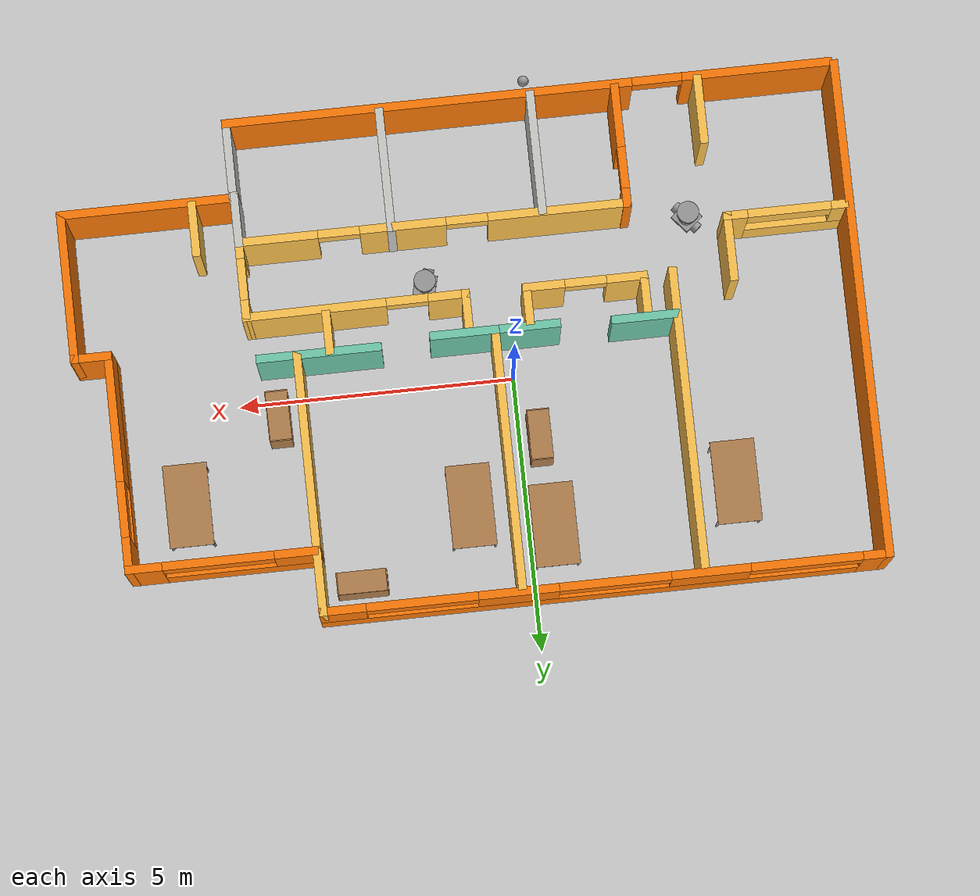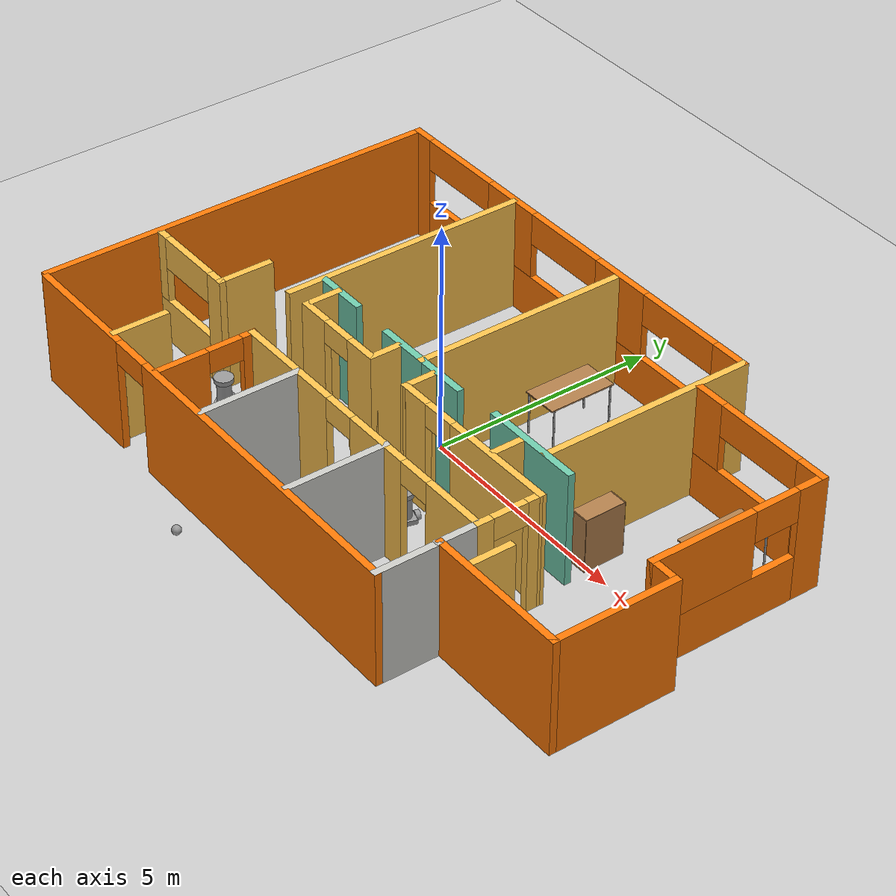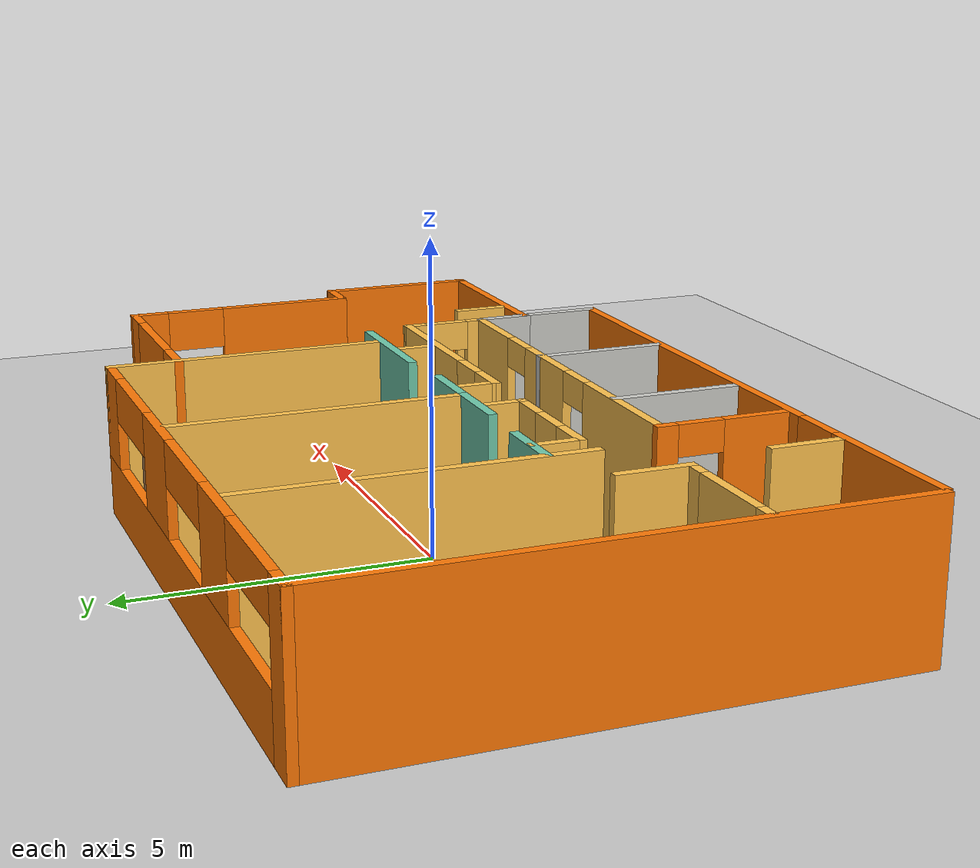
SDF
<sdf version="1.6">
 <world name="default">
  <plugin name="welcome" filename="libhome.so"/>
  <light name="sun" type="directional">
   <pose>0 0 10 0 -0 0</pose>
   <diffuse>0.8 0.8 0.8 1</diffuse>
   <specular>0.2 0.2 0.2 1</specular>
   <attenuation>
    <range>1000</range>
    <constant>0.9</constant>
    <linear>0.01</linear>
    <quadratic>0.001</quadratic>
   </attenuation>
   <direction>-0.5 0.1 -0.9</direction>
  </light>
  <model name="ground_plane">
   <static>1</static>
   <link name="link">
    <collision name="collision">
     <geometry><plane><normal>0 0 1</normal><size>100 100</size></plane></geometry>
     <surface>
      <contact><collide_bitmask>65535</collide_bitmask></contact>
      <friction><ode><mu>100</mu><mu2>50</mu2></ode></friction>
     </surface>
    </collision>
    <visual name="visual">
     <cast_shadows>0</cast_shadows>
     <geometry><plane><normal>0 0 1</normal><size>100 100</size></plane></geometry>
     <material>
      <script><uri>file://media/materials/scripts/gazebo.material</uri><name>Gazebo/Grey</name></script>
     </material>
    </visual>
   </link>
  </model>
  <gravity>0 0 -9.8</gravity>
  <magnetic_field>6e-06 2.3e-05 -4.2e-05</magnetic_field>
  <atmosphere type="adiabatic"/>
  <physics name="default_physics" default="0" type="ode">
   <max_step_size>0.001</max_step_size>
   <real_time_factor>1</real_time_factor>
   <real_time_update_rate>1000</real_time_update_rate>
  </physics>
  <scene><ambient>0.4 0.4 0.4 1</ambient><background>0.7 0.7 0.7 1</background><shadows>1</shadows></scene>
  <spherical_coordinates>
   <surface_model>EARTH_WGS84</surface_model>
   <latitude_deg>0</latitude_deg>
   <longitude_deg>0</longitude_deg>
   <elevation>0</elevation>
   <heading_deg>0</heading_deg>
  </spherical_coordinates>
  <model name="APT916_0">
   <pose>0.75832 -0.376555 0 0 -0 0</pose>
   <link name="Wall_14">
    <collision name="Wall_14_Collision">
     <geometry><box><size>9 0.15 2.5</size></box></geometry>
     <pose>0 0 1.25 0 -0 0</pose>
    </collision>
    <visual name="Wall_14_Visual">
     <pose>0 0 1.25 0 -0 0</pose>
     <geometry><box><size>9 0.15 2.5</size></box></geometry>
     <material>
      <script><uri>file://media/materials/scripts/gazebo.material</uri><name>Gazebo/Grey</name></script>
      <ambient>0.996078 0.47451 0.0196078 1</ambient>
     </material>
     <meta><layer>0</layer></meta>
    </visual>
    <pose>-7.025 0.025 0 0 0 -1.5708</pose>
   </link>
   <link name="Wall_16">
    <collision name="Wall_16_Collision">
     <geometry><box><size>5.5 0.15 2.5</size></box></geometry>
     <pose>0 0 1.25 0 -0 0</pose>
    </collision>
    <visual name="Wall_16_Visual">
     <pose>0 0 1.25 0 -0 0</pose>
     <geometry><box><size>5.5 0.15 2.5</size></box></geometry>
     <material>
      <script><uri>file://media/materials/scripts/gazebo.material</uri><name>Gazebo/Grey</name></script>
      <ambient>1 0.764706 0.305882 1</ambient>
     </material>
     <meta><layer>0</layer></meta>
    </visual>
    <pose>-3.747 1.703 0 0 0 -1.5708</pose>
   </link>
   <link name="Wall_18">
    <collision name="Wall_18_Collision">
     <geometry><box><size>1.25 0.15 2.5</size></box></geometry>
     <pose>0 0 1.25 0 -0 0</pose>
    </collision>
    <visual name="Wall_18_Visual">
     <pose>0 0 1.25 0 -0 0</pose>
     <geometry><box><size>1.25 0.15 2.5</size></box></geometry>
     <material>
      <script><uri>file://media/materials/scripts/gazebo.material</uri><name>Gazebo/Grey</name></script>
      <ambient>1 0.764706 0.305882 1</ambient>
     </material>
     <meta><layer>0</layer></meta>
    </visual>
    <pose>-4.824 -1.31 0 0 0 -1.5708</pose>
   </link>
   <link name="Wall_19">
    <pose>-5.874 -1.86 0 0 -0 3.14159</pose>
    <visual name="Wall_19_Visual_0">
     <pose>-0.90386 0 1.25 0 -0 0</pose>
     <geometry><box><size>0.442281 0.15 2.5</size></box></geometry>
     <material>
      <script><uri>file://media/materials/scripts/gazebo.material</uri><name>Gazebo/Grey</name></script>
      <ambient>1 0.764706 0.305882 1</ambient>
     </material>
     <meta><layer>0</layer></meta>
    </visual>
    <collision name="Wall_19_Collision_0">
     <geometry><box><size>0.442281 0.15 2.5</size></box></geometry>
     <pose>-0.90386 0 1.25 0 -0 0</pose>
    </collision>
    <visual name="Wall_19_Visual_1">
     <pose>0.22114 0 0.5 0 -0 0</pose>
     <geometry><box><size>1.80772 0.15 1</size></box></geometry>
     <material>
      <script><uri>file://media/materials/scripts/gazebo.material</uri><name>Gazebo/Grey</name></script>
      <ambient>1 0.764706 0.305882 1</ambient>
     </material>
     <meta><layer>0</layer></meta>
    </visual>
    <collision name="Wall_19_Collision_1">
     <geometry><box><size>1.80772 0.15 1</size></box></geometry>
     <pose>0.22114 0 0.5 0 -0 0</pose>
    </collision>
    <visual name="Wall_19_Visual_2">
     <pose>0.97114 0 1.75 0 -0 0</pose>
     <geometry><box><size>0.307719 0.15 1.5</size></box></geometry>
     <material>
      <script><uri>file://media/materials/scripts/gazebo.material</uri><name>Gazebo/Grey</name></script>
      <ambient>1 0.764706 0.305882 1</ambient>
     </material>
     <meta><layer>0</layer></meta>
    </visual>
    <collision name="Wall_19_Collision_2">
     <geometry><box><size>0.307719 0.15 1.5</size></box></geometry>
     <pose>0.97114 0 1.75 0 -0 0</pose>
    </collision>
    <visual name="Wall_19_Visual_3">
     <pose>0.067281 0 2.15 0 -0 0</pose>
     <geometry><box><size>1.5 0.15 0.7</size></box></geometry>
     <material>
      <script><uri>file://media/materials/scripts/gazebo.material</uri><name>Gazebo/Grey</name></script>
      <ambient>1 0.764706 0.305882 1</ambient>
     </material>
     <meta><layer>0</layer></meta>
    </visual>
    <collision name="Wall_19_Collision_3">
     <geometry><box><size>1.5 0.15 0.7</size></box></geometry>
     <pose>0.067281 0 2.15 0 -0 0</pose>
    </collision>
   </link>
   <link name="Wall_21">
    <collision name="Wall_21_Collision">
     <geometry><box><size>4.75 0.15 2.5</size></box></geometry>
     <pose>0 0 1.25 0 -0 0</pose>
    </collision>
    <visual name="Wall_21_Visual">
     <pose>0 0 1.25 0 -0 0</pose>
     <geometry><box><size>4.75 0.15 2.5</size></box></geometry>
     <material>
      <script><uri>file://media/materials/scripts/gazebo.material</uri><name>Gazebo/Grey</name></script>
      <ambient>1 0.764706 0.305882 1</ambient>
     </material>
     <meta><layer>0</layer></meta>
    </visual>
    <pose>-0.486 2.047 0 0 0 -1.5708</pose>
   </link>
   <link name="Wall_23">
    <collision name="Wall_23_Collision">
     <geometry><box><size>1.25 0.15 2.5</size></box></geometry>
     <pose>0 0 1.25 0 -0 0</pose>
    </collision>
    <visual name="Wall_23_Visual">
     <pose>0 0 1.25 0 -0 0</pose>
     <geometry><box><size>1.25 0.15 2.5</size></box></geometry>
     <material>
      <script><uri>file://media/materials/scripts/gazebo.material</uri><name>Gazebo/Grey</name></script>
      <ambient>0.435294 0.796078 0.67451 1</ambient>
     </material>
     <meta><layer>0</layer></meta>
    </visual>
    <pose>-3.19 -0.206 0 0 -0 3.14159</pose>
   </link>
   <link name="Wall_3">
    <pose>6.425 1.425 0 0 0 -1.5708</pose>
    <visual name="Wall_3_Visual_0">
     <pose>-1.67037 0 1.25 0 -0 0</pose>
     <geometry><box><size>0.659259 0.15 2.5</size></box></geometry>
     <material>
      <script><uri>file://media/materials/scripts/gazebo.material</uri><name>Gazebo/Grey</name></script>
      <ambient>0.996078 0.47451 0.0196078 1</ambient>
     </material>
     <meta><layer>0</layer></meta>
    </visual>
    <collision name="Wall_3_Collision_0">
     <geometry><box><size>0.659259 0.15 2.5</size></box></geometry>
     <pose>-1.67037 0 1.25 0 -0 0</pose>
    </collision>
    <visual name="Wall_3_Visual_1">
     <pose>0.329629 0 0.5 0 -0 0</pose>
     <geometry><box><size>3.34074 0.15 1</size></box></geometry>
     <material>
      <script><uri>file://media/materials/scripts/gazebo.material</uri><name>Gazebo/Grey</name></script>
      <ambient>0.996078 0.47451 0.0196078 1</ambient>
     </material>
     <meta><layer>0</layer></meta>
    </visual>
    <collision name="Wall_3_Collision_1">
     <geometry><box><size>3.34074 0.15 1</size></box></geometry>
     <pose>0.329629 0 0.5 0 -0 0</pose>
    </collision>
    <visual name="Wall_3_Visual_2">
     <pose>0.829629 0 1.75 0 -0 0</pose>
     <geometry><box><size>2.34074 0.15 1.5</size></box></geometry>
     <material>
      <script><uri>file://media/materials/scripts/gazebo.material</uri><name>Gazebo/Grey</name></script>
      <ambient>0.996078 0.47451 0.0196078 1</ambient>
     </material>
     <meta><layer>0</layer></meta>
    </visual>
    <collision name="Wall_3_Collision_2">
     <geometry><box><size>2.34074 0.15 1.5</size></box></geometry>
     <pose>0.829629 0 1.75 0 -0 0</pose>
    </collision>
    <visual name="Wall_3_Visual_3">
     <pose>-0.840741 0 2.15 0 -0 0</pose>
     <geometry><box><size>1 0.15 0.7</size></box></geometry>
     <material>
      <script><uri>file://media/materials/scripts/gazebo.material</uri><name>Gazebo/Grey</name></script>
      <ambient>0.996078 0.47451 0.0196078 1</ambient>
     </material>
     <meta><layer>0</layer></meta>
    </visual>
    <collision name="Wall_3_Collision_3">
     <geometry><box><size>1 0.15 0.7</size></box></geometry>
     <pose>-0.840741 0 2.15 0 -0 0</pose>
    </collision>
   </link>
   <link name="Wall_30">
    <collision name="Wall_30_Collision">
     <geometry><box><size>0.75 0.15 2.5</size></box></geometry>
     <pose>0 0 1.25 0 -0 0</pose>
    </collision>
    <visual name="Wall_30_Visual">
     <pose>0 0 1.25 0 -0 0</pose>
     <geometry><box><size>0.75 0.15 2.5</size></box></geometry>
     <material>
      <script><uri>file://media/materials/scripts/gazebo.material</uri><name>Gazebo/Grey</name></script>
      <ambient>1 0.764706 0.305882 1</ambient>
     </material>
     <meta><layer>0</layer></meta>
    </visual>
    <pose>-3.229 -0.53 0 0 -0 1.5708</pose>
   </link>
   <link name="Wall_32">
    <pose>-2.171 -0.947 0 0 -0 3.14159</pose>
    <visual name="Wall_32_Visual_0">
     <pose>-0.744745 0 1.25 0 -0 0</pose>
     <geometry><box><size>0.76051 0.15 2.5</size></box></geometry>
     <material>
      <script><uri>file://media/materials/scripts/gazebo.material</uri><name>Gazebo/Grey</name></script>
      <ambient>1 0.764706 0.305882 1</ambient>
     </material>
     <meta><layer>0</layer></meta>
    </visual>
    <collision name="Wall_32_Collision_0">
     <geometry><box><size>0.76051 0.15 2.5</size></box></geometry>
     <pose>-0.744745 0 1.25 0 -0 0</pose>
    </collision>
    <visual name="Wall_32_Visual_1">
     <pose>0.755255 0 1.25 0 -0 0</pose>
     <geometry><box><size>0.73949 0.15 2.5</size></box></geometry>
     <material>
      <script><uri>file://media/materials/scripts/gazebo.material</uri><name>Gazebo/Grey</name></script>
      <ambient>1 0.764706 0.305882 1</ambient>
     </material>
     <meta><layer>0</layer></meta>
    </visual>
    <collision name="Wall_32_Collision_1">
     <geometry><box><size>0.73949 0.15 2.5</size></box></geometry>
     <pose>0.755255 0 1.25 0 -0 0</pose>
    </collision>
    <visual name="Wall_32_Visual_2">
     <pose>0.01051 0 2.25 0 -0 0</pose>
     <geometry><box><size>0.75 0.15 0.5</size></box></geometry>
     <material>
      <script><uri>file://media/materials/scripts/gazebo.material</uri><name>Gazebo/Grey</name></script>
      <ambient>1 0.764706 0.305882 1</ambient>
     </material>
     <meta><layer>0</layer></meta>
    </visual>
    <collision name="Wall_32_Collision_2">
     <geometry><box><size>0.75 0.15 0.5</size></box></geometry>
     <pose>0.01051 0 2.25 0 -0 0</pose>
    </collision>
   </link>
   <link name="Wall_35">
    <collision name="Wall_35_Collision">
     <geometry><box><size>1.25 0.15 2.5</size></box></geometry>
     <pose>0 0 1.25 0 -0 0</pose>
    </collision>
    <visual name="Wall_35_Visual">
     <pose>0 0 1.25 0 -0 0</pose>
     <geometry><box><size>1.25 0.15 2.5</size></box></geometry>
     <material>
      <script><uri>file://media/materials/scripts/gazebo.material</uri><name>Gazebo/Grey</name></script>
      <ambient>0.435294 0.796078 0.67451 1</ambient>
     </material>
     <meta><layer>0</layer></meta>
    </visual>
    <pose>-1.036 -0.253 0 0 -0 3.14159</pose>
   </link>
   <link name="Wall_4">
    <collision name="Wall_4_Collision">
     <geometry><box><size>0.75 0.15 2.5</size></box></geometry>
     <pose>0 0 1.25 0 -0 0</pose>
    </collision>
    <visual name="Wall_4_Visual">
     <pose>0 0 1.25 0 -0 0</pose>
     <geometry><box><size>0.75 0.15 2.5</size></box></geometry>
     <material>
      <script><uri>file://media/materials/scripts/gazebo.material</uri><name>Gazebo/Grey</name></script>
      <ambient>0.996078 0.47451 0.0196078 1</ambient>
     </material>
     <meta><layer>0</layer></meta>
    </visual>
    <pose>6.725 -0.5 0 0 -0 0</pose>
   </link>
   <link name="Wall_42">
    <collision name="Wall_42_Collision">
     <geometry><box><size>1.25 0.15 2.5</size></box></geometry>
     <pose>0 0 1.25 0 -0 0</pose>
    </collision>
    <visual name="Wall_42_Visual">
     <pose>0 0 1.25 0 -0 0</pose>
     <geometry><box><size>1.25 0.15 2.5</size></box></geometry>
     <material>
      <script><uri>file://media/materials/scripts/gazebo.material</uri><name>Gazebo/Grey</name></script>
      <ambient>0.435294 0.796078 0.67451 1</ambient>
     </material>
     <meta><layer>0</layer></meta>
    </visual>
    <pose>0.064 -0.253 0 0 -0 3.14159</pose>
   </link>
   <link name="Wall_44">
    <collision name="Wall_44_Collision">
     <geometry><box><size>0.75 0.15 2.5</size></box></geometry>
     <pose>0 0 1.25 0 -0 0</pose>
    </collision>
    <visual name="Wall_44_Visual">
     <pose>0 0 1.25 0 -0 0</pose>
     <geometry><box><size>0.75 0.15 2.5</size></box></geometry>
     <material>
      <script><uri>file://media/materials/scripts/gazebo.material</uri><name>Gazebo/Grey</name></script>
      <ambient>1 0.764706 0.305882 1</ambient>
     </material>
     <meta><layer>0</layer></meta>
    </visual>
    <pose>-0.028 -0.652 0 0 0 -1.5708</pose>
   </link>
   <link name="Wall_5">
    <collision name="Wall_5_Collision">
     <geometry><box><size>2.75 0.15 2.5</size></box></geometry>
     <pose>0 0 1.25 0 -0 0</pose>
    </collision>
    <visual name="Wall_5_Visual">
     <pose>0 0 1.25 0 -0 0</pose>
     <geometry><box><size>2.75 0.15 2.5</size></box></geometry>
     <material>
      <script><uri>file://media/materials/scripts/gazebo.material</uri><name>Gazebo/Grey</name></script>
      <ambient>0.996078 0.47451 0.0196078 1</ambient>
     </material>
     <meta><layer>0</layer></meta>
    </visual>
    <pose>7.025 -1.8 0 0 0 -1.5708</pose>
   </link>
   <link name="Wall_51">
    <collision name="Wall_51_Collision">
     <geometry><box><size>2.25 0.15 2.5</size></box></geometry>
     <pose>0 0 1.25 0 -0 0</pose>
    </collision>
    <visual name="Wall_51_Visual">
     <pose>0 0 1.25 0 -0 0</pose>
     <geometry><box><size>2.25 0.15 2.5</size></box></geometry>
     <material>
      <script><uri>file://media/materials/scripts/gazebo.material</uri><name>Gazebo/Grey</name></script>
      <ambient>0.435294 0.796078 0.67451 1</ambient>
     </material>
     <meta><layer>0</layer></meta>
    </visual>
    <pose>2.684 -0.162 0 0 -0 0</pose>
   </link>
   <link name="Wall_53">
    <pose>-1.975 4.45 0 0 -0 0</pose>
    <visual name="Wall_53_Visual_0">
     <pose>-4.85383 0 1.25 0 -0 0</pose>
     <geometry><box><size>0.542348 0.15 2.5</size></box></geometry>
     <material>
      <script><uri>file://media/materials/scripts/gazebo.material</uri><name>Gazebo/Grey</name></script>
      <ambient>0.996078 0.47451 0.0196078 1</ambient>
     </material>
     <meta><layer>0</layer></meta>
    </visual>
    <collision name="Wall_53_Collision_0">
     <geometry><box><size>0.542348 0.15 2.5</size></box></geometry>
     <pose>-4.85383 0 1.25 0 -0 0</pose>
    </collision>
    <visual name="Wall_53_Visual_1">
     <pose>0.271174 0 0.5 0 -0 0</pose>
     <geometry><box><size>9.70765 0.15 1</size></box></geometry>
     <material>
      <script><uri>file://media/materials/scripts/gazebo.material</uri><name>Gazebo/Grey</name></script>
      <ambient>0.996078 0.47451 0.0196078 1</ambient>
     </material>
     <meta><layer>0</layer></meta>
    </visual>
    <collision name="Wall_53_Collision_1">
     <geometry><box><size>9.70765 0.15 1</size></box></geometry>
     <pose>0.271174 0 0.5 0 -0 0</pose>
    </collision>
    <visual name="Wall_53_Visual_2">
     <pose>-1.87284 0 1.75 0 -0 0</pose>
     <geometry><box><size>1.41962 0.15 1.5</size></box></geometry>
     <material>
      <script><uri>file://media/materials/scripts/gazebo.material</uri><name>Gazebo/Grey</name></script>
      <ambient>0.996078 0.47451 0.0196078 1</ambient>
     </material>
     <meta><layer>0</layer></meta>
    </visual>
    <collision name="Wall_53_Collision_2">
     <geometry><box><size>1.41962 0.15 1.5</size></box></geometry>
     <pose>-1.87284 0 1.75 0 -0 0</pose>
    </collision>
    <visual name="Wall_53_Visual_3">
     <pose>1.55835 0 1.75 0 -0 0</pose>
     <geometry><box><size>1.44277 0.15 1.5</size></box></geometry>
     <material>
      <script><uri>file://media/materials/scripts/gazebo.material</uri><name>Gazebo/Grey</name></script>
      <ambient>0.996078 0.47451 0.0196078 1</ambient>
     </material>
     <meta><layer>0</layer></meta>
    </visual>
    <collision name="Wall_53_Collision_3">
     <geometry><box><size>1.44277 0.15 1.5</size></box></geometry>
     <pose>1.55835 0 1.75 0 -0 0</pose>
    </collision>
    <visual name="Wall_53_Visual_4">
     <pose>4.70237 0 1.75 0 -0 0</pose>
     <geometry><box><size>0.845266 0.15 1.5</size></box></geometry>
     <material>
      <script><uri>file://media/materials/scripts/gazebo.material</uri><name>Gazebo/Grey</name></script>
      <ambient>0.996078 0.47451 0.0196078 1</ambient>
     </material>
     <meta><layer>0</layer></meta>
    </visual>
    <collision name="Wall_53_Collision_4">
     <geometry><box><size>0.845266 0.15 1.5</size></box></geometry>
     <pose>4.70237 0 1.75 0 -0 0</pose>
    </collision>
    <visual name="Wall_53_Visual_5">
     <pose>-3.58265 0 2.15 0 -0 0</pose>
     <geometry><box><size>2 0.15 0.7</size></box></geometry>
     <material>
      <script><uri>file://media/materials/scripts/gazebo.material</uri><name>Gazebo/Grey</name></script>
      <ambient>0.996078 0.47451 0.0196078 1</ambient>
     </material>
     <meta><layer>0</layer></meta>
    </visual>
    <collision name="Wall_53_Collision_5">
     <geometry><box><size>2 0.15 0.7</size></box></geometry>
     <pose>-3.58265 0 2.15 0 -0 0</pose>
    </collision>
    <visual name="Wall_53_Visual_6">
     <pose>-0.163033 0 2.15 0 -0 0</pose>
     <geometry><box><size>2 0.15 0.7</size></box></geometry>
     <material>
      <script><uri>file://media/materials/scripts/gazebo.material</uri><name>Gazebo/Grey</name></script>
      <ambient>0.996078 0.47451 0.0196078 1</ambient>
     </material>
     <meta><layer>0</layer></meta>
    </visual>
    <collision name="Wall_53_Collision_6">
     <geometry><box><size>2 0.15 0.7</size></box></geometry>
     <pose>-0.163033 0 2.15 0 -0 0</pose>
    </collision>
    <visual name="Wall_53_Visual_7">
     <pose>3.27973 0 2.15 0 -0 0</pose>
     <geometry><box><size>2 0.15 0.7</size></box></geometry>
     <material>
      <script><uri>file://media/materials/scripts/gazebo.material</uri><name>Gazebo/Grey</name></script>
      <ambient>0.996078 0.47451 0.0196078 1</ambient>
     </material>
     <meta><layer>0</layer></meta>
    </visual>
    <collision name="Wall_53_Collision_7">
     <geometry><box><size>2 0.15 0.7</size></box></geometry>
     <pose>3.27973 0 2.15 0 -0 0</pose>
    </collision>
   </link>
   <link name="Wall_54">
    <collision name="Wall_54_Collision">
     <geometry><box><size>4.75 0.15 2.5</size></box></geometry>
     <pose>0 0 1.25 0 -0 0</pose>
    </collision>
    <visual name="Wall_54_Visual">
     <pose>0 0 1.25 0 -0 0</pose>
     <geometry><box><size>4.75 0.15 2.5</size></box></geometry>
     <material>
      <script><uri>file://media/materials/scripts/gazebo.material</uri><name>Gazebo/Grey</name></script>
      <ambient>1 0.764706 0.305882 1</ambient>
     </material>
     <meta><layer>0</layer></meta>
    </visual>
    <pose>3.075 2.15 0 0 0 -1.5708</pose>
   </link>
   <link name="Wall_56">
    <pose>4.75 3.35 0 0 -0 3.14159</pose>
    <visual name="Wall_56_Visual_0">
     <pose>-1.41677 0 1.25 0 -0 0</pose>
     <geometry><box><size>0.666459 0.15 2.5</size></box></geometry>
     <material>
      <script><uri>file://media/materials/scripts/gazebo.material</uri><name>Gazebo/Grey</name></script>
      <ambient>0.996078 0.47451 0.0196078 1</ambient>
     </material>
     <meta><layer>0</layer></meta>
    </visual>
    <collision name="Wall_56_Collision_0">
     <geometry><box><size>0.666459 0.15 2.5</size></box></geometry>
     <pose>-1.41677 0 1.25 0 -0 0</pose>
    </collision>
    <visual name="Wall_56_Visual_1">
     <pose>0.333229 0 0.5 0 -0 0</pose>
     <geometry><box><size>2.83354 0.15 1</size></box></geometry>
     <material>
      <script><uri>file://media/materials/scripts/gazebo.material</uri><name>Gazebo/Grey</name></script>
      <ambient>0.996078 0.47451 0.0196078 1</ambient>
     </material>
     <meta><layer>0</layer></meta>
    </visual>
    <collision name="Wall_56_Collision_1">
     <geometry><box><size>2.83354 0.15 1</size></box></geometry>
     <pose>0.333229 0 0.5 0 -0 0</pose>
    </collision>
    <visual name="Wall_56_Visual_2">
     <pose>1.33323 0 1.75 0 -0 0</pose>
     <geometry><box><size>0.833541 0.15 1.5</size></box></geometry>
     <material>
      <script><uri>file://media/materials/scripts/gazebo.material</uri><name>Gazebo/Grey</name></script>
      <ambient>0.996078 0.47451 0.0196078 1</ambient>
     </material>
     <meta><layer>0</layer></meta>
    </visual>
    <collision name="Wall_56_Collision_2">
     <geometry><box><size>0.833541 0.15 1.5</size></box></geometry>
     <pose>1.33323 0 1.75 0 -0 0</pose>
    </collision>
    <visual name="Wall_56_Visual_3">
     <pose>-0.083541 0 2.15 0 -0 0</pose>
     <geometry><box><size>2 0.15 0.7</size></box></geometry>
     <material>
      <script><uri>file://media/materials/scripts/gazebo.material</uri><name>Gazebo/Grey</name></script>
      <ambient>0.996078 0.47451 0.0196078 1</ambient>
     </material>
     <meta><layer>0</layer></meta>
    </visual>
    <collision name="Wall_56_Collision_3">
     <geometry><box><size>2 0.15 0.7</size></box></geometry>
     <pose>-0.083541 0 2.15 0 -0 0</pose>
    </collision>
   </link>
   <link name="Wall_58">
    <collision name="Wall_58_Collision">
     <geometry><box><size>0.8 0.15 2.5</size></box></geometry>
     <pose>0 0 1.25 0 -0 0</pose>
    </collision>
    <visual name="Wall_58_Visual">
     <pose>0 0 1.25 0 -0 0</pose>
     <geometry><box><size>0.8 0.15 2.5</size></box></geometry>
     <material>
      <script><uri>file://media/materials/scripts/gazebo.material</uri><name>Gazebo/Grey</name></script>
      <ambient>1 0.764706 0.305882 1</ambient>
     </material>
     <meta><layer>0</layer></meta>
    </visual>
    <pose>2.486 -0.51 0 0 0 -1.5708</pose>
   </link>
   <link name="Wall_6">
    <collision name="Wall_6_Collision">
     <geometry><box><size>3.25 0.15 2.5</size></box></geometry>
     <pose>0 0 1.25 0 -0 0</pose>
    </collision>
    <visual name="Wall_6_Visual">
     <pose>0 0 1.25 0 -0 0</pose>
     <geometry><box><size>3.25 0.15 2.5</size></box></geometry>
     <material>
      <script><uri>file://media/materials/scripts/gazebo.material</uri><name>Gazebo/Grey</name></script>
      <ambient>0.996078 0.47451 0.0196078 1</ambient>
     </material>
     <meta><layer>0</layer></meta>
    </visual>
    <pose>5.475 -3.1 0 0 -0 3.14159</pose>
   </link>
   <link name="Wall_60">
    <collision name="Wall_60_Collision">
     <geometry><box><size>1.25 0.15 2.5</size></box></geometry>
     <pose>0 0 1.25 0 -0 0</pose>
    </collision>
    <visual name="Wall_60_Visual">
     <pose>0 0 1.25 0 -0 0</pose>
     <geometry><box><size>1.25 0.15 2.5</size></box></geometry>
     <material>
      <script><uri>file://media/materials/scripts/gazebo.material</uri><name>Gazebo/Grey</name></script>
      <ambient>1 0.764706 0.305882 1</ambient>
     </material>
     <meta><layer>0</layer></meta>
    </visual>
    <pose>-4.563 -3.832 0 0 -0 1.5708</pose>
   </link>
   <link name="Wall_63">
    <pose>0.371 -2.285 0 0 -0 0</pose>
    <visual name="Wall_63_Visual_0">
     <pose>-2.21806 0 1.25 0 -0 0</pose>
     <geometry><box><size>2.56389 0.15 2.5</size></box></geometry>
     <material>
      <script><uri>file://media/materials/scripts/gazebo.material</uri><name>Gazebo/Grey</name></script>
      <ambient>1 0.764706 0.305882 1</ambient>
     </material>
     <meta><layer>0</layer></meta>
    </visual>
    <collision name="Wall_63_Collision_0">
     <geometry><box><size>2.56389 0.15 2.5</size></box></geometry>
     <pose>-2.21806 0 1.25 0 -0 0</pose>
    </collision>
    <visual name="Wall_63_Visual_1">
     <pose>0.590236 0 1.25 0 -0 0</pose>
     <geometry><box><size>1.5527 0.15 2.5</size></box></geometry>
     <material>
      <script><uri>file://media/materials/scripts/gazebo.material</uri><name>Gazebo/Grey</name></script>
      <ambient>1 0.764706 0.305882 1</ambient>
     </material>
     <meta><layer>0</layer></meta>
    </visual>
    <collision name="Wall_63_Collision_1">
     <geometry><box><size>1.5527 0.15 2.5</size></box></geometry>
     <pose>0.590236 0 1.25 0 -0 0</pose>
    </collision>
    <visual name="Wall_63_Visual_2">
     <pose>2.80829 0 1.25 0 -0 0</pose>
     <geometry><box><size>1.38342 0.15 2.5</size></box></geometry>
     <material>
      <script><uri>file://media/materials/scripts/gazebo.material</uri><name>Gazebo/Grey</name></script>
      <ambient>1 0.764706 0.305882 1</ambient>
     </material>
     <meta><layer>0</layer></meta>
    </visual>
    <collision name="Wall_63_Collision_2">
     <geometry><box><size>1.38342 0.15 2.5</size></box></geometry>
     <pose>2.80829 0 1.25 0 -0 0</pose>
    </collision>
    <visual name="Wall_63_Visual_3">
     <pose>-0.561112 0 2.25 0 -0 0</pose>
     <geometry><box><size>0.75 0.15 0.5</size></box></geometry>
     <material>
      <script><uri>file://media/materials/scripts/gazebo.material</uri><name>Gazebo/Grey</name></script>
      <ambient>1 0.764706 0.305882 1</ambient>
     </material>
     <meta><layer>0</layer></meta>
    </visual>
    <collision name="Wall_63_Collision_3">
     <geometry><box><size>0.75 0.15 0.5</size></box></geometry>
     <pose>-0.561112 0 2.25 0 -0 0</pose>
    </collision>
    <visual name="Wall_63_Visual_4">
     <pose>1.74158 0 2.25 0 -0 0</pose>
     <geometry><box><size>0.75 0.15 0.5</size></box></geometry>
     <material>
      <script><uri>file://media/materials/scripts/gazebo.material</uri><name>Gazebo/Grey</name></script>
      <ambient>1 0.764706 0.305882 1</ambient>
     </material>
     <meta><layer>0</layer></meta>
    </visual>
    <collision name="Wall_63_Collision_4">
     <geometry><box><size>0.75 0.15 0.5</size></box></geometry>
     <pose>1.74158 0 2.25 0 -0 0</pose>
    </collision>
   </link>
   <link name="Wall_66">
    <pose>-3.07 -3.324 0 0 -0 1.5708</pose>
    <visual name="Wall_66_Visual_0">
     <pose>-0.549177 0 1.25 0 -0 0</pose>
     <geometry><box><size>1.15165 0.15 2.5</size></box></geometry>
     <material>
      <script><uri>file://media/materials/scripts/gazebo.material</uri><name>Gazebo/Grey</name></script>
      <ambient>0.996078 0.47451 0.0196078 1</ambient>
     </material>
     <meta><layer>0</layer></meta>
    </visual>
    <collision name="Wall_66_Collision_0">
     <geometry><box><size>1.15165 0.15 2.5</size></box></geometry>
     <pose>-0.549177 0 1.25 0 -0 0</pose>
    </collision>
    <visual name="Wall_66_Visual_1">
     <pose>0.950823 0 1.25 0 -0 0</pose>
     <geometry><box><size>0.348354 0.15 2.5</size></box></geometry>
     <material>
      <script><uri>file://media/materials/scripts/gazebo.material</uri><name>Gazebo/Grey</name></script>
      <ambient>0.996078 0.47451 0.0196078 1</ambient>
     </material>
     <meta><layer>0</layer></meta>
    </visual>
    <collision name="Wall_66_Collision_1">
     <geometry><box><size>0.348354 0.15 2.5</size></box></geometry>
     <pose>0.950823 0 1.25 0 -0 0</pose>
    </collision>
    <visual name="Wall_66_Visual_2">
     <pose>0.401646 0 2.25 0 -0 0</pose>
     <geometry><box><size>0.75 0.15 0.5</size></box></geometry>
     <material>
      <script><uri>file://media/materials/scripts/gazebo.material</uri><name>Gazebo/Grey</name></script>
      <ambient>0.996078 0.47451 0.0196078 1</ambient>
     </material>
     <meta><layer>0</layer></meta>
    </visual>
    <collision name="Wall_66_Collision_2">
     <geometry><box><size>0.75 0.15 0.5</size></box></geometry>
     <pose>0.401646 0 2.25 0 -0 0</pose>
    </collision>
   </link>
   <link name="Wall_68">
    <collision name="Wall_68_Collision">
     <geometry><box><size>1 0.15 2.5</size></box></geometry>
     <pose>0 0 1.25 0 -0 0</pose>
    </collision>
    <visual name="Wall_68_Visual">
     <pose>0 0 1.25 0 -0 0</pose>
     <geometry><box><size>1 0.15 2.5</size></box></geometry>
     <material>
      <script><uri>file://media/materials/scripts/gazebo.material</uri><name>Gazebo/Grey</name></script>
      <ambient>1 0.764706 0.305882 1</ambient>
     </material>
     <meta><layer>0</layer></meta>
    </visual>
    <pose>4.676 -2.615 0 0 0 -1.5708</pose>
   </link>
   <link name="Wall_7">
    <collision name="Wall_7_Collision">
     <geometry><box><size>1.5 0.15 2.5</size></box></geometry>
     <pose>0 0 1.25 0 -0 0</pose>
    </collision>
    <visual name="Wall_7_Visual">
     <pose>0 0 1.25 0 -0 0</pose>
     <geometry><box><size>1.5 0.15 2.5</size></box></geometry>
     <material>
      <script><uri>file://media/materials/scripts/gazebo.material</uri><name>Gazebo/CeilingTiled</name></script>
      <ambient>1 1 1 1</ambient>
     </material>
     <meta><layer>0</layer></meta>
    </visual>
    <pose>3.925 -3.775 0 0 0 -1.5708</pose>
   </link>
   <link name="Wall_71">
    <collision name="Wall_71_Collision">
     <geometry><box><size>1 0.15 2.5</size></box></geometry>
     <pose>0 0 1.25 0 -0 0</pose>
    </collision>
    <visual name="Wall_71_Visual">
     <pose>0 0 1.25 0 -0 0</pose>
     <geometry><box><size>1 0.15 2.5</size></box></geometry>
     <material>
      <script><uri>file://media/materials/scripts/gazebo.material</uri><name>Gazebo/CeilingTiled</name></script>
      <ambient>1 1 1 1</ambient>
     </material>
     <meta><layer>0</layer></meta>
    </visual>
    <pose>3.906 -2.705 0 0 0 -1.5708</pose>
   </link>
   <link name="Wall_73">
    <collision name="Wall_73_Collision">
     <geometry><box><size>0.75 0.15 2.5</size></box></geometry>
     <pose>0 0 1.25 0 -0 0</pose>
    </collision>
    <visual name="Wall_73_Visual">
     <pose>0 0 1.25 0 -0 0</pose>
     <geometry><box><size>0.75 0.15 2.5</size></box></geometry>
     <material>
      <script><uri>file://media/materials/scripts/gazebo.material</uri><name>Gazebo/Grey</name></script>
      <ambient>1 0.764706 0.305882 1</ambient>
     </material>
     <meta><layer>0</layer></meta>
    </visual>
    <pose>-1.121 -0.647 0 0 -0 1.5708</pose>
   </link>
   <link name="Wall_77">
    <pose>3.906 -1.605 0 0 -0 1.5708</pose>
    <visual name="Wall_77_Visual_0">
     <pose>-0.570824 0 1.25 0 -0 0</pose>
     <geometry><box><size>0.358352 0.15 2.5</size></box></geometry>
     <material>
      <script><uri>file://media/materials/scripts/gazebo.material</uri><name>Gazebo/Grey</name></script>
      <ambient>1 0.764706 0.305882 1</ambient>
     </material>
     <meta><layer>0</layer></meta>
    </visual>
    <collision name="Wall_77_Collision_0">
     <geometry><box><size>0.358352 0.15 2.5</size></box></geometry>
     <pose>-0.570824 0 1.25 0 -0 0</pose>
    </collision>
    <visual name="Wall_77_Visual_1">
     <pose>0.554176 0 1.25 0 -0 0</pose>
     <geometry><box><size>0.391648 0.15 2.5</size></box></geometry>
     <material>
      <script><uri>file://media/materials/scripts/gazebo.material</uri><name>Gazebo/Grey</name></script>
      <ambient>1 0.764706 0.305882 1</ambient>
     </material>
     <meta><layer>0</layer></meta>
    </visual>
    <collision name="Wall_77_Collision_1">
     <geometry><box><size>0.391648 0.15 2.5</size></box></geometry>
     <pose>0.554176 0 1.25 0 -0 0</pose>
    </collision>
    <visual name="Wall_77_Visual_2">
     <pose>-0.016648 0 2.25 0 -0 0</pose>
     <geometry><box><size>0.75 0.15 0.5</size></box></geometry>
     <material>
      <script><uri>file://media/materials/scripts/gazebo.material</uri><name>Gazebo/Grey</name></script>
      <ambient>1 0.764706 0.305882 1</ambient>
     </material>
     <meta><layer>0</layer></meta>
    </visual>
    <collision name="Wall_77_Collision_2">
     <geometry><box><size>0.75 0.15 0.5</size></box></geometry>
     <pose>-0.016648 0 2.25 0 -0 0</pose>
    </collision>
   </link>
   <link name="Wall_78">
    <pose>1.939 -0.941 0 0 0 -3.136</pose>
    <visual name="Wall_78_Visual_0">
     <pose>-0.750321 0 1.25 0 -0 0</pose>
     <geometry><box><size>2.58332 0.15 2.5</size></box></geometry>
     <material>
      <script><uri>file://media/materials/scripts/gazebo.material</uri><name>Gazebo/Grey</name></script>
      <ambient>1 0.764706 0.305882 1</ambient>
     </material>
     <meta><layer>0</layer></meta>
    </visual>
    <collision name="Wall_78_Collision_0">
     <geometry><box><size>2.58332 0.15 2.5</size></box></geometry>
     <pose>-0.750321 0 1.25 0 -0 0</pose>
    </collision>
    <visual name="Wall_78_Visual_1">
     <pose>1.66666 0 1.25 0 -0 0</pose>
     <geometry><box><size>0.750642 0.15 2.5</size></box></geometry>
     <material>
      <script><uri>file://media/materials/scripts/gazebo.material</uri><name>Gazebo/Grey</name></script>
      <ambient>1 0.764706 0.305882 1</ambient>
     </material>
     <meta><layer>0</layer></meta>
    </visual>
    <collision name="Wall_78_Collision_1">
     <geometry><box><size>0.750642 0.15 2.5</size></box></geometry>
     <pose>1.66666 0 1.25 0 -0 0</pose>
    </collision>
    <visual name="Wall_78_Visual_2">
     <pose>0.91634 0 2.25 0 -0 0</pose>
     <geometry><box><size>0.75 0.15 0.5</size></box></geometry>
     <material>
      <script><uri>file://media/materials/scripts/gazebo.material</uri><name>Gazebo/Grey</name></script>
      <ambient>1 0.764706 0.305882 1</ambient>
     </material>
     <meta><layer>0</layer></meta>
    </visual>
    <collision name="Wall_78_Collision_2">
     <geometry><box><size>0.75 0.15 0.5</size></box></geometry>
     <pose>0.91634 0 2.25 0 -0 0</pose>
    </collision>
   </link>
   <link name="Wall_8">
    <pose>-1.5 -4.45 0 0 -0 3.14159</pose>
    <visual name="Wall_8_Visual_0">
     <pose>-1.80553 0 1.25 0 -0 0</pose>
     <geometry><box><size>7.38895 0.15 2.5</size></box></geometry>
     <material>
      <script><uri>file://media/materials/scripts/gazebo.material</uri><name>Gazebo/Grey</name></script>
      <ambient>0.996078 0.47451 0.0196078 1</ambient>
     </material>
     <meta><layer>0</layer></meta>
    </visual>
    <collision name="Wall_8_Collision_0">
     <geometry><box><size>7.38895 0.15 2.5</size></box></geometry>
     <pose>-1.80553 0 1.25 0 -0 0</pose>
    </collision>
    <visual name="Wall_8_Visual_1">
     <pose>4.14447 0 1.25 0 -0 0</pose>
     <geometry><box><size>2.71105 0.15 2.5</size></box></geometry>
     <material>
      <script><uri>file://media/materials/scripts/gazebo.material</uri><name>Gazebo/Grey</name></script>
      <ambient>0.996078 0.47451 0.0196078 1</ambient>
     </material>
     <meta><layer>0</layer></meta>
    </visual>
    <collision name="Wall_8_Collision_1">
     <geometry><box><size>2.71105 0.15 2.5</size></box></geometry>
     <pose>4.14447 0 1.25 0 -0 0</pose>
    </collision>
    <visual name="Wall_8_Visual_2">
     <pose>2.33895 0 2.25 0 -0 0</pose>
     <geometry><box><size>0.9 0.15 0.5</size></box></geometry>
     <material>
      <script><uri>file://media/materials/scripts/gazebo.material</uri><name>Gazebo/Grey</name></script>
      <ambient>0.996078 0.47451 0.0196078 1</ambient>
     </material>
     <meta><layer>0</layer></meta>
    </visual>
    <collision name="Wall_8_Collision_2">
     <geometry><box><size>0.9 0.15 0.5</size></box></geometry>
     <pose>2.33895 0 2.25 0 -0 0</pose>
    </collision>
   </link>
   <link name="Wall_80">
    <collision name="Wall_80_Collision">
     <geometry><box><size>2.25 0.15 2.5</size></box></geometry>
     <pose>0 0 1.25 0 -0 0</pose>
    </collision>
    <visual name="Wall_80_Visual">
     <pose>0 0 1.25 0 -0 0</pose>
     <geometry><box><size>2.25 0.15 2.5</size></box></geometry>
     <material>
      <script><uri>file://media/materials/scripts/gazebo.material</uri><name>Gazebo/CeilingTiled</name></script>
      <ambient>1 1 1 1</ambient>
     </material>
     <meta><layer>0</layer></meta>
    </visual>
    <pose>-1.55027 -3.3569 0 0 0 -1.5708</pose>
   </link>
   <link name="Wall_82">
    <collision name="Wall_82_Collision">
     <geometry><box><size>2.25 0.15 2.5</size></box></geometry>
     <pose>0 0 1.25 0 -0 0</pose>
    </collision>
    <visual name="Wall_82_Visual">
     <pose>0 0 1.25 0 -0 0</pose>
     <geometry><box><size>2.25 0.15 2.5</size></box></geometry>
     <material>
      <script><uri>file://media/materials/scripts/gazebo.material</uri><name>Gazebo/CeilingTiled</name></script>
      <ambient>1 1 1 1</ambient>
     </material>
     <meta><layer>0</layer></meta>
    </visual>
    <pose>1.1711 -3.32699 0 0 0 -1.5708</pose>
   </link>
   <static>1</static>
  </model>
  <model name="table">
   <static>1</static>
   <link name="link">
    <collision name="surface">
     <pose>0 0 1 0 -0 0</pose>
     <geometry><box><size>1.5 0.8 0.03</size></box></geometry>
     <surface><friction><ode><mu>0.6</mu><mu2>0.6</mu2></ode></friction></surface>
    </collision>
    <visual name="visual1">
     <pose>0 0 1 0 -0 0</pose>
     <geometry><box><size>1.5 0.8 0.03</size></box></geometry>
     <material>
      <script><uri>file://media/materials/scripts/gazebo.material</uri><name>Gazebo/Wood</name></script>
     </material>
    </visual>
    <collision name="front_left_leg">
     <pose>0.68 0.38 0.5 0 -0 0</pose>
     <geometry><cylinder><radius>0.02</radius><length>1</length></cylinder></geometry>
    </collision>
    <visual name="front_left_leg">
     <pose>0.68 0.38 0.5 0 -0 0</pose>
     <geometry><cylinder><radius>0.02</radius><length>1</length></cylinder></geometry>
     <material>
      <script><uri>file://media/materials/scripts/gazebo.material</uri><name>Gazebo/Grey</name></script>
     </material>
    </visual>
    <collision name="front_right_leg">
     <pose>0.68 -0.38 0.5 0 -0 0</pose>
     <geometry><cylinder><radius>0.02</radius><length>1</length></cylinder></geometry>
    </collision>
    <visual name="front_right_leg">
     <pose>0.68 -0.38 0.5 0 -0 0</pose>
     <geometry><cylinder><radius>0.02</radius><length>1</length></cylinder></geometry>
     <material>
      <script><uri>file://media/materials/scripts/gazebo.material</uri><name>Gazebo/Grey</name></script>
     </material>
    </visual>
    <collision name="back_right_leg">
     <pose>-0.68 -0.38 0.5 0 -0 0</pose>
     <geometry><cylinder><radius>0.02</radius><length>1</length></cylinder></geometry>
    </collision>
    <visual name="back_right_leg">
     <pose>-0.68 -0.38 0.5 0 -0 0</pose>
     <geometry><cylinder><radius>0.02</radius><length>1</length></cylinder></geometry>
     <material>
      <script><uri>file://media/materials/scripts/gazebo.material</uri><name>Gazebo/Grey</name></script>
     </material>
    </visual>
    <collision name="back_left_leg">
     <pose>-0.68 0.38 0.5 0 -0 0</pose>
     <geometry><cylinder><radius>0.02</radius><length>1</length></cylinder></geometry>
    </collision>
    <visual name="back_left_leg">
     <pose>-0.68 0.38 0.5 0 -0 0</pose>
     <geometry><cylinder><radius>0.02</radius><length>1</length></cylinder></geometry>
     <material>
      <script><uri>file://media/materials/scripts/gazebo.material</uri><name>Gazebo/Grey</name></script>
     </material>
    </visual>
   </link>
   <pose>6.08075 1.78031 0 0 -0 1.57</pose>
  </model>
  <model name="table_clone">
   <static>1</static>
   <link name="link">
    <collision name="surface">
     <pose>0 0 1 0 -0 0</pose>
     <geometry><box><size>1.5 0.8 0.03</size></box></geometry>
     <surface><friction><ode><mu>0.6</mu><mu2>0.6</mu2></ode></friction></surface>
    </collision>
    <visual name="visual1">
     <pose>0 0 1 0 -0 0</pose>
     <geometry><box><size>1.5 0.8 0.03</size></box></geometry>
     <material>
      <script><uri>file://media/materials/scripts/gazebo.material</uri><name>Gazebo/Wood</name></script>
     </material>
    </visual>
    <collision name="front_left_leg">
     <pose>0.68 0.38 0.5 0 -0 0</pose>
     <geometry><cylinder><radius>0.02</radius><length>1</length></cylinder></geometry>
    </collision>
    <visual name="front_left_leg">
     <pose>0.68 0.38 0.5 0 -0 0</pose>
     <geometry><cylinder><radius>0.02</radius><length>1</length></cylinder></geometry>
     <material>
      <script><uri>file://media/materials/scripts/gazebo.material</uri><name>Gazebo/Grey</name></script>
     </material>
    </visual>
    <collision name="front_right_leg">
     <pose>0.68 -0.38 0.5 0 -0 0</pose>
     <geometry><cylinder><radius>0.02</radius><length>1</length></cylinder></geometry>
    </collision>
    <visual name="front_right_leg">
     <pose>0.68 -0.38 0.5 0 -0 0</pose>
     <geometry><cylinder><radius>0.02</radius><length>1</length></cylinder></geometry>
     <material>
      <script><uri>file://media/materials/scripts/gazebo.material</uri><name>Gazebo/Grey</name></script>
     </material>
    </visual>
    <collision name="back_right_leg">
     <pose>-0.68 -0.38 0.5 0 -0 0</pose>
     <geometry><cylinder><radius>0.02</radius><length>1</length></cylinder></geometry>
    </collision>
    <visual name="back_right_leg">
     <pose>-0.68 -0.38 0.5 0 -0 0</pose>
     <geometry><cylinder><radius>0.02</radius><length>1</length></cylinder></geometry>
     <material>
      <script><uri>file://media/materials/scripts/gazebo.material</uri><name>Gazebo/Grey</name></script>
     </material>
    </visual>
    <collision name="back_left_leg">
     <pose>-0.68 0.38 0.5 0 -0 0</pose>
     <geometry><cylinder><radius>0.02</radius><length>1</length></cylinder></geometry>
    </collision>
    <visual name="back_left_leg">
     <pose>-0.68 0.38 0.5 0 -0 0</pose>
     <geometry><cylinder><radius>0.02</radius><length>1</length></cylinder></geometry>
     <material>
      <script><uri>file://media/materials/scripts/gazebo.material</uri><name>Gazebo/Grey</name></script>
     </material>
    </visual>
   </link>
   <pose>-0.445123 2.80854 0 0 -0 1.57</pose>
  </model>
  <model name="table_clone_0">
   <static>1</static>
   <link name="link">
    <collision name="surface">
     <pose>0 0 1 0 -0 0</pose>
     <geometry><box><size>1.5 0.8 0.03</size></box></geometry>
     <surface><friction><ode><mu>0.6</mu><mu2>0.6</mu2></ode></friction></surface>
    </collision>
    <visual name="visual1">
     <pose>0 0 1 0 -0 0</pose>
     <geometry><box><size>1.5 0.8 0.03</size></box></geometry>
     <material>
      <script><uri>file://media/materials/scripts/gazebo.material</uri><name>Gazebo/Wood</name></script>
     </material>
    </visual>
    <collision name="front_left_leg">
     <pose>0.68 0.38 0.5 0 -0 0</pose>
     <geometry><cylinder><radius>0.02</radius><length>1</length></cylinder></geometry>
    </collision>
    <visual name="front_left_leg">
     <pose>0.68 0.38 0.5 0 -0 0</pose>
     <geometry><cylinder><radius>0.02</radius><length>1</length></cylinder></geometry>
     <material>
      <script><uri>file://media/materials/scripts/gazebo.material</uri><name>Gazebo/Grey</name></script>
     </material>
    </visual>
    <collision name="front_right_leg">
     <pose>0.68 -0.38 0.5 0 -0 0</pose>
     <geometry><cylinder><radius>0.02</radius><length>1</length></cylinder></geometry>
    </collision>
    <visual name="front_right_leg">
     <pose>0.68 -0.38 0.5 0 -0 0</pose>
     <geometry><cylinder><radius>0.02</radius><length>1</length></cylinder></geometry>
     <material>
      <script><uri>file://media/materials/scripts/gazebo.material</uri><name>Gazebo/Grey</name></script>
     </material>
    </visual>
    <collision name="back_right_leg">
     <pose>-0.68 -0.38 0.5 0 -0 0</pose>
     <geometry><cylinder><radius>0.02</radius><length>1</length></cylinder></geometry>
    </collision>
    <visual name="back_right_leg">
     <pose>-0.68 -0.38 0.5 0 -0 0</pose>
     <geometry><cylinder><radius>0.02</radius><length>1</length></cylinder></geometry>
     <material>
      <script><uri>file://media/materials/scripts/gazebo.material</uri><name>Gazebo/Grey</name></script>
     </material>
    </visual>
    <collision name="back_left_leg">
     <pose>-0.68 0.38 0.5 0 -0 0</pose>
     <geometry><cylinder><radius>0.02</radius><length>1</length></cylinder></geometry>
    </collision>
    <visual name="back_left_leg">
     <pose>-0.68 0.38 0.5 0 -0 0</pose>
     <geometry><cylinder><radius>0.02</radius><length>1</length></cylinder></geometry>
     <material>
      <script><uri>file://media/materials/scripts/gazebo.material</uri><name>Gazebo/Grey</name></script>
     </material>
    </visual>
   </link>
   <pose>1.01497 2.31628 0 0 -0 1.57</pose>
  </model>
  <model name="table_clone_1">
   <static>1</static>
   <link name="link">
    <collision name="surface">
     <pose>0 0 1 0 -0 0</pose>
     <geometry><box><size>1.5 0.8 0.03</size></box></geometry>
     <surface><friction><ode><mu>0.6</mu><mu2>0.6</mu2></ode></friction></surface>
    </collision>
    <visual name="visual1">
     <pose>0 0 1 0 -0 0</pose>
     <geometry><box><size>1.5 0.8 0.03</size></box></geometry>
     <material>
      <script><uri>file://media/materials/scripts/gazebo.material</uri><name>Gazebo/Wood</name></script>
     </material>
    </visual>
    <collision name="front_left_leg">
     <pose>0.68 0.38 0.5 0 -0 0</pose>
     <geometry><cylinder><radius>0.02</radius><length>1</length></cylinder></geometry>
    </collision>
    <visual name="front_left_leg">
     <pose>0.68 0.38 0.5 0 -0 0</pose>
     <geometry><cylinder><radius>0.02</radius><length>1</length></cylinder></geometry>
     <material>
      <script><uri>file://media/materials/scripts/gazebo.material</uri><name>Gazebo/Grey</name></script>
     </material>
    </visual>
    <collision name="front_right_leg">
     <pose>0.68 -0.38 0.5 0 -0 0</pose>
     <geometry><cylinder><radius>0.02</radius><length>1</length></cylinder></geometry>
    </collision>
    <visual name="front_right_leg">
     <pose>0.68 -0.38 0.5 0 -0 0</pose>
     <geometry><cylinder><radius>0.02</radius><length>1</length></cylinder></geometry>
     <material>
      <script><uri>file://media/materials/scripts/gazebo.material</uri><name>Gazebo/Grey</name></script>
     </material>
    </visual>
    <collision name="back_right_leg">
     <pose>-0.68 -0.38 0.5 0 -0 0</pose>
     <geometry><cylinder><radius>0.02</radius><length>1</length></cylinder></geometry>
    </collision>
    <visual name="back_right_leg">
     <pose>-0.68 -0.38 0.5 0 -0 0</pose>
     <geometry><cylinder><radius>0.02</radius><length>1</length></cylinder></geometry>
     <material>
      <script><uri>file://media/materials/scripts/gazebo.material</uri><name>Gazebo/Grey</name></script>
     </material>
    </visual>
    <collision name="back_left_leg">
     <pose>-0.68 0.38 0.5 0 -0 0</pose>
     <geometry><cylinder><radius>0.02</radius><length>1</length></cylinder></geometry>
    </collision>
    <visual name="back_left_leg">
     <pose>-0.68 0.38 0.5 0 -0 0</pose>
     <geometry><cylinder><radius>0.02</radius><length>1</length></cylinder></geometry>
     <material>
      <script><uri>file://media/materials/scripts/gazebo.material</uri><name>Gazebo/Grey</name></script>
     </material>
    </visual>
   </link>
   <pose>-3.78233 2.37452 0 0 -0 1.57</pose>
  </model>
  <model name="bookshelf">
   <static>1</static>
   <link name="link">
    <inertial><mass>1</mass></inertial>
    <collision name="back">
     <pose>0 0.005 0.6 0 -0 0</pose>
     <geometry><box><size>0.9 0.01 1.2</size></box></geometry>
    </collision>
    <visual name="visual1">
     <pose>0 0.005 0.6 0 -0 0</pose>
     <geometry><box><size>0.9 0.01 1.2</size></box></geometry>
     <material>
      <script><uri>file://media/materials/scripts/gazebo.material</uri><name>Gazebo/Wood</name></script>
     </material>
    </visual>
    <collision name="left_side">
     <pose>0.45 -0.195 0.6 0 -0 0</pose>
     <geometry><box><size>0.02 0.4 1.2</size></box></geometry>
    </collision>
    <visual name="visual2">
     <pose>0.45 -0.195 0.6 0 -0 0</pose>
     <geometry><box><size>0.02 0.4 1.2</size></box></geometry>
     <material>
      <script><uri>file://media/materials/scripts/gazebo.material</uri><name>Gazebo/Wood</name></script>
     </material>
    </visual>
    <collision name="right_side">
     <pose>-0.45 -0.195 0.6 0 -0 0</pose>
     <geometry><box><size>0.02 0.4 1.2</size></box></geometry>
    </collision>
    <visual name="visual3">
     <pose>-0.45 -0.195 0.6 0 -0 0</pose>
     <geometry><box><size>0.02 0.4 1.2</size></box></geometry>
     <material>
      <script><uri>file://media/materials/scripts/gazebo.material</uri><name>Gazebo/Wood</name></script>
     </material>
    </visual>
    <collision name="bottom">
     <pose>0 -0.195 0.03 0 -0 0</pose>
     <geometry><box><size>0.88 0.4 0.06</size></box></geometry>
    </collision>
    <visual name="visual4">
     <pose>0 -0.195 0.03 0 -0 0</pose>
     <geometry><box><size>0.88 0.4 0.06</size></box></geometry>
     <material>
      <script><uri>file://media/materials/scripts/gazebo.material</uri><name>Gazebo/Wood</name></script>
     </material>
    </visual>
    <collision name="top">
     <pose>0 -0.195 1.19 0 -0 0</pose>
     <geometry><box><size>0.88 0.4 0.02</size></box></geometry>
    </collision>
    <visual name="visual5">
     <pose>0 -0.195 1.19 0 -0 0</pose>
     <geometry><box><size>0.88 0.4 0.02</size></box></geometry>
     <material>
      <script><uri>file://media/materials/scripts/gazebo.material</uri><name>Gazebo/Wood</name></script>
     </material>
    </visual>
    <collision name="low_shelf">
     <pose>0 -0.195 0.43 0 -0 0</pose>
     <geometry><box><size>0.88 0.4 0.02</size></box></geometry>
    </collision>
    <visual name="visual6">
     <pose>0 -0.195 0.43 0 -0 0</pose>
     <geometry><box><size>0.88 0.4 0.02</size></box></geometry>
     <material>
      <script><uri>file://media/materials/scripts/gazebo.material</uri><name>Gazebo/Wood</name></script>
     </material>
    </visual>
    <collision name="high_shelf">
     <pose>0 -0.195 0.8 0 -0 0</pose>
     <geometry><box><size>0.88 0.4 0.02</size></box></geometry>
    </collision>
    <visual name="visual7">
     <pose>0 -0.195 0.8 0 -0 0</pose>
     <geometry><box><size>0.88 0.4 0.02</size></box></geometry>
     <material>
      <script><uri>file://media/materials/scripts/gazebo.material</uri><name>Gazebo/Wood</name></script>
     </material>
    </visual>
   </link>
   <pose>3.10362 3.68906 0 0 -0 0</pose>
  </model>
  <model name="bookshelf_0">
   <static>1</static>
   <link name="link">
    <inertial><mass>1</mass></inertial>
    <collision name="back">
     <pose>0 0.005 0.6 0 -0 0</pose>
     <geometry><box><size>0.9 0.01 1.2</size></box></geometry>
    </collision>
    <visual name="visual1">
     <pose>0 0.005 0.6 0 -0 0</pose>
     <geometry><box><size>0.9 0.01 1.2</size></box></geometry>
     <material>
      <script><uri>file://media/materials/scripts/gazebo.material</uri><name>Gazebo/Wood</name></script>
     </material>
    </visual>
    <collision name="left_side">
     <pose>0.45 -0.195 0.6 0 -0 0</pose>
     <geometry><box><size>0.02 0.4 1.2</size></box></geometry>
    </collision>
    <visual name="visual2">
     <pose>0.45 -0.195 0.6 0 -0 0</pose>
     <geometry><box><size>0.02 0.4 1.2</size></box></geometry>
     <material>
      <script><uri>file://media/materials/scripts/gazebo.material</uri><name>Gazebo/Wood</name></script>
     </material>
    </visual>
    <collision name="right_side">
     <pose>-0.45 -0.195 0.6 0 -0 0</pose>
     <geometry><box><size>0.02 0.4 1.2</size></box></geometry>
    </collision>
    <visual name="visual3">
     <pose>-0.45 -0.195 0.6 0 -0 0</pose>
     <geometry><box><size>0.02 0.4 1.2</size></box></geometry>
     <material>
      <script><uri>file://media/materials/scripts/gazebo.material</uri><name>Gazebo/Wood</name></script>
     </material>
    </visual>
    <collision name="bottom">
     <pose>0 -0.195 0.03 0 -0 0</pose>
     <geometry><box><size>0.88 0.4 0.06</size></box></geometry>
    </collision>
    <visual name="visual4">
     <pose>0 -0.195 0.03 0 -0 0</pose>
     <geometry><box><size>0.88 0.4 0.06</size></box></geometry>
     <material>
      <script><uri>file://media/materials/scripts/gazebo.material</uri><name>Gazebo/Wood</name></script>
     </material>
    </visual>
    <collision name="top">
     <pose>0 -0.195 1.19 0 -0 0</pose>
     <geometry><box><size>0.88 0.4 0.02</size></box></geometry>
    </collision>
    <visual name="visual5">
     <pose>0 -0.195 1.19 0 -0 0</pose>
     <geometry><box><size>0.88 0.4 0.02</size></box></geometry>
     <material>
      <script><uri>file://media/materials/scripts/gazebo.material</uri><name>Gazebo/Wood</name></script>
     </material>
    </visual>
    <collision name="low_shelf">
     <pose>0 -0.195 0.43 0 -0 0</pose>
     <geometry><box><size>0.88 0.4 0.02</size></box></geometry>
    </collision>
    <visual name="visual6">
     <pose>0 -0.195 0.43 0 -0 0</pose>
     <geometry><box><size>0.88 0.4 0.02</size></box></geometry>
     <material>
      <script><uri>file://media/materials/scripts/gazebo.material</uri><name>Gazebo/Wood</name></script>
     </material>
    </visual>
    <collision name="high_shelf">
     <pose>0 -0.195 0.8 0 -0 0</pose>
     <geometry><box><size>0.88 0.4 0.02</size></box></geometry>
    </collision>
    <visual name="visual7">
     <pose>0 -0.195 0.8 0 -0 0</pose>
     <geometry><box><size>0.88 0.4 0.02</size></box></geometry>
     <material>
      <script><uri>file://media/materials/scripts/gazebo.material</uri><name>Gazebo/Wood</name></script>
     </material>
    </visual>
   </link>
   <pose>-0.161686 1.17476 0 0 0 -1.57</pose>
  </model>
  <model name="bookshelf_1">
   <static>1</static>
   <link name="link">
    <inertial><mass>1</mass></inertial>
    <collision name="back">
     <pose>0 0.005 0.6 0 -0 0</pose>
     <geometry><box><size>0.9 0.01 1.2</size></box></geometry>
    </collision>
    <visual name="visual1">
     <pose>0 0.005 0.6 0 -0 0</pose>
     <geometry><box><size>0.9 0.01 1.2</size></box></geometry>
     <material>
      <script><uri>file://media/materials/scripts/gazebo.material</uri><name>Gazebo/Wood</name></script>
     </material>
    </visual>
    <collision name="left_side">
     <pose>0.45 -0.195 0.6 0 -0 0</pose>
     <geometry><box><size>0.02 0.4 1.2</size></box></geometry>
    </collision>
    <visual name="visual2">
     <pose>0.45 -0.195 0.6 0 -0 0</pose>
     <geometry><box><size>0.02 0.4 1.2</size></box></geometry>
     <material>
      <script><uri>file://media/materials/scripts/gazebo.material</uri><name>Gazebo/Wood</name></script>
     </material>
    </visual>
    <collision name="right_side">
     <pose>-0.45 -0.195 0.6 0 -0 0</pose>
     <geometry><box><size>0.02 0.4 1.2</size></box></geometry>
    </collision>
    <visual name="visual3">
     <pose>-0.45 -0.195 0.6 0 -0 0</pose>
     <geometry><box><size>0.02 0.4 1.2</size></box></geometry>
     <material>
      <script><uri>file://media/materials/scripts/gazebo.material</uri><name>Gazebo/Wood</name></script>
     </material>
    </visual>
    <collision name="bottom">
     <pose>0 -0.195 0.03 0 -0 0</pose>
     <geometry><box><size>0.88 0.4 0.06</size></box></geometry>
    </collision>
    <visual name="visual4">
     <pose>0 -0.195 0.03 0 -0 0</pose>
     <geometry><box><size>0.88 0.4 0.06</size></box></geometry>
     <material>
      <script><uri>file://media/materials/scripts/gazebo.material</uri><name>Gazebo/Wood</name></script>
     </material>
    </visual>
    <collision name="top">
     <pose>0 -0.195 1.19 0 -0 0</pose>
     <geometry><box><size>0.88 0.4 0.02</size></box></geometry>
    </collision>
    <visual name="visual5">
     <pose>0 -0.195 1.19 0 -0 0</pose>
     <geometry><box><size>0.88 0.4 0.02</size></box></geometry>
     <material>
      <script><uri>file://media/materials/scripts/gazebo.material</uri><name>Gazebo/Wood</name></script>
     </material>
    </visual>
    <collision name="low_shelf">
     <pose>0 -0.195 0.43 0 -0 0</pose>
     <geometry><box><size>0.88 0.4 0.02</size></box></geometry>
    </collision>
    <visual name="visual6">
     <pose>0 -0.195 0.43 0 -0 0</pose>
     <geometry><box><size>0.88 0.4 0.02</size></box></geometry>
     <material>
      <script><uri>file://media/materials/scripts/gazebo.material</uri><name>Gazebo/Wood</name></script>
     </material>
    </visual>
    <collision name="high_shelf">
     <pose>0 -0.195 0.8 0 -0 0</pose>
     <geometry><box><size>0.88 0.4 0.02</size></box></geometry>
    </collision>
    <visual name="visual7">
     <pose>0 -0.195 0.8 0 -0 0</pose>
     <geometry><box><size>0.88 0.4 0.02</size></box></geometry>
     <material>
      <script><uri>file://media/materials/scripts/gazebo.material</uri><name>Gazebo/Wood</name></script>
     </material>
    </visual>
   </link>
   <pose>4.49492 0.351304 0 0 0 -1.56329</pose>
  </model>
  <model name="ServeronWheels">
   <link name="link_4">
    <pose>1.37401 -0.876349 0.5 1.5e-05 1e-06 -0.001069</pose>
    <inertial>
     <mass>1</mass>
     <inertia>
      <ixx>0.166667</ixx>
      <ixy>0</ixy>
      <ixz>0</ixz>
      <iyy>0.166667</iyy>
      <iyz>0</iyz>
      <izz>0.166667</izz>
     </inertia>
    </inertial>
    <visual name="visual">
     <geometry><box><size>0.4 0.4 0.1</size></box></geometry>
     <material>
      <lighting>1</lighting>
      <script><uri>file://media/materials/scripts/gazebo.material</uri><name>Gazebo/Grey</name></script>
      <shader type="pixel"><normal_map>__default__</normal_map></shader>
      <ambient>0.3 0.3 0.3 1</ambient>
      <diffuse>0.7 0.7 0.7 1</diffuse>
      <specular>0.01 0.01 0.01 1</specular>
      <emissive>0 0 0 1</emissive>
     </material>
    </visual>
    <collision name="collision">
     <geometry><box><size>0.4 0.4 0.1</size></box></geometry>
     <surface>
      <friction>
       <ode><mu>1</mu><mu2>1</mu2><fdir1>0 0 0</fdir1><slip1>0</slip1><slip2>0</slip2></ode>
       <torsional>
        <coefficient>1</coefficient>
        <patch_radius>0</patch_radius>
        <surface_radius>0</surface_radius>
        <use_patch_radius>1</use_patch_radius>
        <ode><slip>0</slip></ode>
       </torsional>
      </friction>
      <bounce><restitution_coefficient>0</restitution_coefficient><threshold>1e+06</threshold></bounce>
      <contact>
       <collide_without_contact>0</collide_without_contact>
       <collide_without_contact_bitmask>1</collide_without_contact_bitmask>
       <collide_bitmask>1</collide_bitmask>
       <ode>
        <soft_cfm>0</soft_cfm>
        <soft_erp>0.2</soft_erp>
        <kp>1e+13</kp>
        <kd>1</kd>
        <max_vel>0.01</max_vel>
        <min_depth>0</min_depth>
       </ode>
       <bullet>
        <split_impulse>1</split_impulse>
        <split_impulse_penetration_threshold>-0.01</split_impulse_penetration_threshold>
        <soft_cfm>0</soft_cfm>
        <soft_erp>0.2</soft_erp>
        <kp>1e+13</kp>
        <kd>1</kd>
       </bullet>
      </contact>
     </surface>
    </collision>
   </link>
   <link name="link_0">
    <pose>1.22401 -0.876187 0.425001 0 -0 0</pose>
    <inertial>
     <mass>1</mass>
     <inertia><ixx>0.1</ixx><ixy>0</ixy><ixz>0</ixz><iyy>0.1</iyy><iyz>0</iyz><izz>0.1</izz></inertia>
    </inertial>
    <visual name="visual">
     <geometry><sphere><radius>0.025</radius></sphere></geometry>
     <material>
      <lighting>1</lighting>
      <script><uri>file://media/materials/scripts/gazebo.material</uri><name>Gazebo/Grey</name></script>
      <shader type="pixel"><normal_map>__default__</normal_map></shader>
      <ambient>0.3 0.3 0.3 1</ambient>
      <diffuse>0.7 0.7 0.7 1</diffuse>
      <specular>0.01 0.01 0.01 1</specular>
      <emissive>0 0 0 1</emissive>
     </material>
    </visual>
    <collision name="collision">
     <geometry><sphere><radius>0.025</radius></sphere></geometry>
     <surface>
      <friction>
       <ode><mu>1</mu><mu2>1</mu2><fdir1>0 0 0</fdir1><slip1>0</slip1><slip2>0</slip2></ode>
       <torsional>
        <coefficient>1</coefficient>
        <patch_radius>0</patch_radius>
        <surface_radius>0</surface_radius>
        <use_patch_radius>1</use_patch_radius>
        <ode><slip>0</slip></ode>
       </torsional>
      </friction>
      <bounce><restitution_coefficient>0</restitution_coefficient><threshold>1e+06</threshold></bounce>
      <contact>
       <collide_without_contact>0</collide_without_contact>
       <collide_without_contact_bitmask>1</collide_without_contact_bitmask>
       <collide_bitmask>1</collide_bitmask>
       <ode>
        <soft_cfm>0</soft_cfm>
        <soft_erp>0.2</soft_erp>
        <kp>1e+13</kp>
        <kd>1</kd>
        <max_vel>0.01</max_vel>
        <min_depth>0</min_depth>
       </ode>
       <bullet>
        <split_impulse>1</split_impulse>
        <split_impulse_penetration_threshold>-0.01</split_impulse_penetration_threshold>
        <soft_cfm>0</soft_cfm>
        <soft_erp>0.2</soft_erp>
        <kp>1e+13</kp>
        <kd>1</kd>
       </bullet>
      </contact>
     </surface>
    </collision>
   </link>
   <link name="link_0_clone">
    <pose>1.52401 -0.876509 0.425 0 -0 0</pose>
    <inertial>
     <mass>1</mass>
     <inertia><ixx>0.1</ixx><ixy>0</ixy><ixz>0</ixz><iyy>0.1</iyy><iyz>0</iyz><izz>0.1</izz></inertia>
    </inertial>
    <visual name="visual">
     <geometry><sphere><radius>0.025</radius></sphere></geometry>
     <material>
      <lighting>1</lighting>
      <script><uri>file://media/materials/scripts/gazebo.material</uri><name>Gazebo/Grey</name></script>
      <shader type="pixel"><normal_map>__default__</normal_map></shader>
      <ambient>0.3 0.3 0.3 1</ambient>
      <diffuse>0.7 0.7 0.7 1</diffuse>
      <specular>0.01 0.01 0.01 1</specular>
      <emissive>0 0 0 1</emissive>
     </material>
    </visual>
    <collision name="collision">
     <geometry><sphere><radius>0.025</radius></sphere></geometry>
     <surface>
      <friction>
       <ode><mu>1</mu><mu2>1</mu2><fdir1>0 0 0</fdir1><slip1>0</slip1><slip2>0</slip2></ode>
       <torsional>
        <coefficient>1</coefficient>
        <patch_radius>0</patch_radius>
        <surface_radius>0</surface_radius>
        <use_patch_radius>1</use_patch_radius>
        <ode><slip>0</slip></ode>
       </torsional>
      </friction>
      <bounce><restitution_coefficient>0</restitution_coefficient><threshold>1e+06</threshold></bounce>
      <contact>
       <collide_without_contact>0</collide_without_contact>
       <collide_without_contact_bitmask>1</collide_without_contact_bitmask>
       <collide_bitmask>1</collide_bitmask>
       <ode>
        <soft_cfm>0</soft_cfm>
        <soft_erp>0.2</soft_erp>
        <kp>1e+13</kp>
        <kd>1</kd>
        <max_vel>0.01</max_vel>
        <min_depth>0</min_depth>
       </ode>
       <bullet>
        <split_impulse>1</split_impulse>
        <split_impulse_penetration_threshold>-0.01</split_impulse_penetration_threshold>
        <soft_cfm>0</soft_cfm>
        <soft_erp>0.2</soft_erp>
        <kp>1e+13</kp>
        <kd>1</kd>
       </bullet>
      </contact>
     </surface>
    </collision>
   </link>
   <link name="link_5">
    <pose>1.35374 -1.12644 0.499883 1.57 1e-06 -0.001069</pose>
    <inertial>
     <mass>1</mass>
     <inertia><ixx>0.145833</ixx><ixy>0</ixy><ixz>0</ixz><iyy>0.145833</iyy><iyz>0</iyz><izz>0.125</izz></inertia>
    </inertial>
    <visual name="visual">
     <geometry><cylinder><radius>0.1</radius><length>0.1</length></cylinder></geometry>
     <material>
      <lighting>1</lighting>
      <script><uri>file://media/materials/scripts/gazebo.material</uri><name>Gazebo/Grey</name></script>
      <shader type="pixel"><normal_map>__default__</normal_map></shader>
      <ambient>0.3 0.3 0.3 1</ambient>
      <diffuse>0.7 0.7 0.7 1</diffuse>
      <specular>0.01 0.01 0.01 1</specular>
      <emissive>0 0 0 1</emissive>
     </material>
    </visual>
    <collision name="collision">
     <geometry><cylinder><radius>0.1</radius><length>0.1</length></cylinder></geometry>
     <surface>
      <friction>
       <ode><mu>1</mu><mu2>1</mu2><fdir1>0 0 0</fdir1><slip1>0</slip1><slip2>0</slip2></ode>
       <torsional>
        <coefficient>1</coefficient>
        <patch_radius>0</patch_radius>
        <surface_radius>0</surface_radius>
        <use_patch_radius>1</use_patch_radius>
        <ode><slip>0</slip></ode>
       </torsional>
      </friction>
      <bounce><restitution_coefficient>0</restitution_coefficient><threshold>1e+06</threshold></bounce>
      <contact>
       <collide_without_contact>0</collide_without_contact>
       <collide_without_contact_bitmask>1</collide_without_contact_bitmask>
       <collide_bitmask>1</collide_bitmask>
       <ode>
        <soft_cfm>0</soft_cfm>
        <soft_erp>0.2</soft_erp>
        <kp>1e+13</kp>
        <kd>1</kd>
        <max_vel>0.01</max_vel>
        <min_depth>0</min_depth>
       </ode>
       <bullet>
        <split_impulse>1</split_impulse>
        <split_impulse_penetration_threshold>-0.01</split_impulse_penetration_threshold>
        <soft_cfm>0</soft_cfm>
        <soft_erp>0.2</soft_erp>
        <kp>1e+13</kp>
        <kd>1</kd>
       </bullet>
      </contact>
     </surface>
    </collision>
   </link>
   <link name="link_5_clone">
    <pose>1.37428 -0.626162 0.499988 1.57001 2e-06 -0.002138</pose>
    <inertial>
     <mass>1</mass>
     <inertia><ixx>0.145833</ixx><ixy>0</ixy><ixz>0</ixz><iyy>0.145833</iyy><iyz>0</iyz><izz>0.125</izz></inertia>
    </inertial>
    <visual name="visual">
     <geometry><cylinder><radius>0.1</radius><length>0.1</length></cylinder></geometry>
     <material>
      <lighting>1</lighting>
      <script><uri>file://media/materials/scripts/gazebo.material</uri><name>Gazebo/Grey</name></script>
      <shader type="pixel"><normal_map>__default__</normal_map></shader>
      <ambient>0.3 0.3 0.3 1</ambient>
      <diffuse>0.7 0.7 0.7 1</diffuse>
      <specular>0.01 0.01 0.01 1</specular>
      <emissive>0 0 0 1</emissive>
     </material>
    </visual>
    <collision name="collision">
     <geometry><cylinder><radius>0.1</radius><length>0.1</length></cylinder></geometry>
     <surface>
      <friction>
       <ode><mu>1</mu><mu2>1</mu2><fdir1>0 0 0</fdir1><slip1>0</slip1><slip2>0</slip2></ode>
       <torsional>
        <coefficient>1</coefficient>
        <patch_radius>0</patch_radius>
        <surface_radius>0</surface_radius>
        <use_patch_radius>1</use_patch_radius>
        <ode><slip>0</slip></ode>
       </torsional>
      </friction>
      <bounce><restitution_coefficient>0</restitution_coefficient><threshold>1e+06</threshold></bounce>
      <contact>
       <collide_without_contact>0</collide_without_contact>
       <collide_without_contact_bitmask>1</collide_without_contact_bitmask>
       <collide_bitmask>1</collide_bitmask>
       <ode>
        <soft_cfm>0</soft_cfm>
        <soft_erp>0.2</soft_erp>
        <kp>1e+13</kp>
        <kd>1</kd>
        <max_vel>0.01</max_vel>
        <min_depth>0</min_depth>
       </ode>
       <bullet>
        <split_impulse>1</split_impulse>
        <split_impulse_penetration_threshold>-0.01</split_impulse_penetration_threshold>
        <soft_cfm>0</soft_cfm>
        <soft_erp>0.2</soft_erp>
        <kp>1e+13</kp>
        <kd>1</kd>
       </bullet>
      </contact>
     </surface>
    </collision>
   </link>
   <link name="link_5_clone_clone">
    <pose>1.37401 -0.876353 0.799991 0 3e-06 -0.003207</pose>
    <inertial>
     <mass>1</mass>
     <inertia><ixx>0.145833</ixx><ixy>0</ixy><ixz>0</ixz><iyy>0.145833</iyy><iyz>0</iyz><izz>0.125</izz></inertia>
    </inertial>
    <visual name="visual">
     <geometry><cylinder><radius>0.15</radius><length>0.5</length></cylinder></geometry>
     <material>
      <lighting>1</lighting>
      <script><uri>file://media/materials/scripts/gazebo.material</uri><name>Gazebo/Grey</name></script>
      <shader type="pixel"><normal_map>__default__</normal_map></shader>
      <ambient>0.3 0.3 0.3 1</ambient>
      <diffuse>0.7 0.7 0.7 1</diffuse>
      <specular>0.01 0.01 0.01 1</specular>
      <emissive>0 0 0 1</emissive>
     </material>
    </visual>
    <collision name="collision">
     <geometry><cylinder><radius>0.15</radius><length>0.5</length></cylinder></geometry>
     <surface>
      <friction>
       <ode><mu>1</mu><mu2>1</mu2><fdir1>0 0 0</fdir1><slip1>0</slip1><slip2>0</slip2></ode>
       <torsional>
        <coefficient>1</coefficient>
        <patch_radius>0</patch_radius>
        <surface_radius>0</surface_radius>
        <use_patch_radius>1</use_patch_radius>
        <ode><slip>0</slip></ode>
       </torsional>
      </friction>
      <bounce><restitution_coefficient>0</restitution_coefficient><threshold>1e+06</threshold></bounce>
      <contact>
       <collide_without_contact>0</collide_without_contact>
       <collide_without_contact_bitmask>1</collide_without_contact_bitmask>
       <collide_bitmask>1</collide_bitmask>
       <ode>
        <soft_cfm>0</soft_cfm>
        <soft_erp>0.2</soft_erp>
        <kp>1e+13</kp>
        <kd>1</kd>
        <max_vel>0.01</max_vel>
        <min_depth>0</min_depth>
       </ode>
       <bullet>
        <split_impulse>1</split_impulse>
        <split_impulse_penetration_threshold>-0.01</split_impulse_penetration_threshold>
        <soft_cfm>0</soft_cfm>
        <soft_erp>0.2</soft_erp>
        <kp>1e+13</kp>
        <kd>1</kd>
       </bullet>
      </contact>
     </surface>
    </collision>
   </link>
   <link name="link_5_clone_clone_clone">
    <pose>1.37401 -0.876358 1.1 1.5e-05 4e-06 -0.004276</pose>
    <inertial>
     <mass>1</mass>
     <inertia><ixx>0.145833</ixx><ixy>0</ixy><ixz>0</ixz><iyy>0.145833</iyy><iyz>0</iyz><izz>0.125</izz></inertia>
    </inertial>
    <visual name="visual">
     <geometry><cylinder><radius>0.2</radius><length>0.1</length></cylinder></geometry>
     <material>
      <lighting>1</lighting>
      <script><uri>file://media/materials/scripts/gazebo.material</uri><name>Gazebo/Grey</name></script>
      <shader type="pixel"><normal_map>__default__</normal_map></shader>
      <ambient>0.3 0.3 0.3 1</ambient>
      <diffuse>0.7 0.7 0.7 1</diffuse>
      <specular>0.01 0.01 0.01 1</specular>
      <emissive>0 0 0 1</emissive>
     </material>
    </visual>
    <collision name="collision">
     <geometry><cylinder><radius>0.2</radius><length>0.1</length></cylinder></geometry>
     <surface>
      <friction>
       <ode><mu>1</mu><mu2>1</mu2><fdir1>0 0 0</fdir1><slip1>0</slip1><slip2>0</slip2></ode>
       <torsional>
        <coefficient>1</coefficient>
        <patch_radius>0</patch_radius>
        <surface_radius>0</surface_radius>
        <use_patch_radius>1</use_patch_radius>
        <ode><slip>0</slip></ode>
       </torsional>
      </friction>
      <bounce><restitution_coefficient>0</restitution_coefficient><threshold>1e+06</threshold></bounce>
      <contact>
       <collide_without_contact>0</collide_without_contact>
       <collide_without_contact_bitmask>1</collide_without_contact_bitmask>
       <collide_bitmask>1</collide_bitmask>
       <ode>
        <soft_cfm>0</soft_cfm>
        <soft_erp>0.2</soft_erp>
        <kp>1e+13</kp>
        <kd>1</kd>
        <max_vel>0.01</max_vel>
        <min_depth>0</min_depth>
       </ode>
       <bullet>
        <split_impulse>1</split_impulse>
        <split_impulse_penetration_threshold>-0.01</split_impulse_penetration_threshold>
        <soft_cfm>0</soft_cfm>
        <soft_erp>0.2</soft_erp>
        <kp>1e+13</kp>
        <kd>1</kd>
       </bullet>
      </contact>
     </surface>
    </collision>
   </link>
   <joint name="link_4_JOINT_1" type="ball">
    <parent>link_4</parent>
    <child>link_0_clone</child>
    <physics>
     <ode><limit><cfm>0</cfm><erp>0.2</erp></limit><suspension><cfm>0</cfm><erp>0.2</erp></suspension></ode>
    </physics>
   </joint>
   <joint name="link_4_JOINT_4_0" type="ball">
    <parent>link_4</parent>
    <child>link_0</child>
    <physics>
     <ode><limit><cfm>0</cfm><erp>0.2</erp></limit><suspension><cfm>0</cfm><erp>0.2</erp></suspension></ode>
    </physics>
   </joint>
   <joint name="link_4_JOINT_4" type="revolute">
    <parent>link_4</parent>
    <child>link_5</child>
    <axis>
     <xyz>0 0 1</xyz>
     <use_parent_model_frame>0</use_parent_model_frame>
     <limit>
      <lower>-1.79769e+308</lower>
      <upper>1.79769e+308</upper>
      <effort>-1</effort>
      <velocity>-1</velocity>
     </limit>
     <dynamics>
      <spring_reference>0</spring_reference>
      <spring_stiffness>0</spring_stiffness>
      <damping>0</damping>
      <friction>0</friction>
     </dynamics>
    </axis>
    <physics>
     <ode><limit><cfm>0</cfm><erp>0.2</erp></limit><suspension><cfm>0</cfm><erp>0.2</erp></suspension></ode>
    </physics>
   </joint>
   <joint name="link_4_JOINT_5" type="revolute">
    <parent>link_4</parent>
    <child>link_5_clone</child>
    <axis>
     <xyz>0 0 1</xyz>
     <use_parent_model_frame>0</use_parent_model_frame>
     <limit><lower>-1e+16</lower><upper>1e+16</upper><effort>-1</effort><velocity>-1</velocity></limit>
     <dynamics>
      <spring_reference>0</spring_reference>
      <spring_stiffness>0</spring_stiffness>
      <damping>0</damping>
      <friction>0</friction>
     </dynamics>
    </axis>
    <physics>
     <ode><limit><cfm>0</cfm><erp>0.2</erp></limit><suspension><cfm>0</cfm><erp>0.2</erp></suspension></ode>
    </physics>
   </joint>
   <joint name="link_4_JOINT_6" type="fixed">
    <parent>link_4</parent>
    <child>link_5_clone_clone</child>
    <physics>
     <ode><limit><cfm>0</cfm><erp>0.2</erp></limit><suspension><cfm>0</cfm><erp>0.2</erp></suspension></ode>
    </physics>
   </joint>
   <joint name="link_5_clone_clone_JOINT_7" type="fixed">
    <parent>link_5_clone_clone</parent>
    <child>link_5_clone_clone_clone</child>
    <physics>
     <ode><limit><cfm>0</cfm><erp>0.2</erp></limit><suspension><cfm>0</cfm><erp>0.2</erp></suspension></ode>
    </physics>
   </joint>
   <static>0</static>
   <pose>-1.85729 -2.39912 -0.399088 -0.000181 0.000702 -2.42882</pose>
  </model>
  <model name="ServeronWheels_0">
   <link name="link_4">
    <pose>1.37401 -0.876349 0.5 1.5e-05 1e-06 -0.001069</pose>
    <inertial>
     <mass>1</mass>
     <inertia>
      <ixx>0.166667</ixx>
      <ixy>0</ixy>
      <ixz>0</ixz>
      <iyy>0.166667</iyy>
      <iyz>0</iyz>
      <izz>0.166667</izz>
     </inertia>
    </inertial>
    <visual name="visual">
     <geometry><box><size>0.4 0.4 0.1</size></box></geometry>
     <material>
      <lighting>1</lighting>
      <script><uri>file://media/materials/scripts/gazebo.material</uri><name>Gazebo/Grey</name></script>
      <shader type="pixel"><normal_map>__default__</normal_map></shader>
      <ambient>0.3 0.3 0.3 1</ambient>
      <diffuse>0.7 0.7 0.7 1</diffuse>
      <specular>0.01 0.01 0.01 1</specular>
      <emissive>0 0 0 1</emissive>
     </material>
    </visual>
    <collision name="collision">
     <geometry><box><size>0.4 0.4 0.1</size></box></geometry>
     <surface>
      <friction>
       <ode><mu>1</mu><mu2>1</mu2><fdir1>0 0 0</fdir1><slip1>0</slip1><slip2>0</slip2></ode>
       <torsional>
        <coefficient>1</coefficient>
        <patch_radius>0</patch_radius>
        <surface_radius>0</surface_radius>
        <use_patch_radius>1</use_patch_radius>
        <ode><slip>0</slip></ode>
       </torsional>
      </friction>
      <bounce><restitution_coefficient>0</restitution_coefficient><threshold>1e+06</threshold></bounce>
      <contact>
       <collide_without_contact>0</collide_without_contact>
       <collide_without_contact_bitmask>1</collide_without_contact_bitmask>
       <collide_bitmask>1</collide_bitmask>
       <ode>
        <soft_cfm>0</soft_cfm>
        <soft_erp>0.2</soft_erp>
        <kp>1e+13</kp>
        <kd>1</kd>
        <max_vel>0.01</max_vel>
        <min_depth>0</min_depth>
       </ode>
       <bullet>
        <split_impulse>1</split_impulse>
        <split_impulse_penetration_threshold>-0.01</split_impulse_penetration_threshold>
        <soft_cfm>0</soft_cfm>
        <soft_erp>0.2</soft_erp>
        <kp>1e+13</kp>
        <kd>1</kd>
       </bullet>
      </contact>
     </surface>
    </collision>
   </link>
   <link name="link_0">
    <pose>1.22401 -0.876187 0.425001 0 -0 0</pose>
    <inertial>
     <mass>1</mass>
     <inertia><ixx>0.1</ixx><ixy>0</ixy><ixz>0</ixz><iyy>0.1</iyy><iyz>0</iyz><izz>0.1</izz></inertia>
    </inertial>
    <visual name="visual">
     <geometry><sphere><radius>0.025</radius></sphere></geometry>
     <material>
      <lighting>1</lighting>
      <script><uri>file://media/materials/scripts/gazebo.material</uri><name>Gazebo/Grey</name></script>
      <shader type="pixel"><normal_map>__default__</normal_map></shader>
      <ambient>0.3 0.3 0.3 1</ambient>
      <diffuse>0.7 0.7 0.7 1</diffuse>
      <specular>0.01 0.01 0.01 1</specular>
      <emissive>0 0 0 1</emissive>
     </material>
    </visual>
    <collision name="collision">
     <geometry><sphere><radius>0.025</radius></sphere></geometry>
     <surface>
      <friction>
       <ode><mu>1</mu><mu2>1</mu2><fdir1>0 0 0</fdir1><slip1>0</slip1><slip2>0</slip2></ode>
       <torsional>
        <coefficient>1</coefficient>
        <patch_radius>0</patch_radius>
        <surface_radius>0</surface_radius>
        <use_patch_radius>1</use_patch_radius>
        <ode><slip>0</slip></ode>
       </torsional>
      </friction>
      <bounce><restitution_coefficient>0</restitution_coefficient><threshold>1e+06</threshold></bounce>
      <contact>
       <collide_without_contact>0</collide_without_contact>
       <collide_without_contact_bitmask>1</collide_without_contact_bitmask>
       <collide_bitmask>1</collide_bitmask>
       <ode>
        <soft_cfm>0</soft_cfm>
        <soft_erp>0.2</soft_erp>
        <kp>1e+13</kp>
        <kd>1</kd>
        <max_vel>0.01</max_vel>
        <min_depth>0</min_depth>
       </ode>
       <bullet>
        <split_impulse>1</split_impulse>
        <split_impulse_penetration_threshold>-0.01</split_impulse_penetration_threshold>
        <soft_cfm>0</soft_cfm>
        <soft_erp>0.2</soft_erp>
        <kp>1e+13</kp>
        <kd>1</kd>
       </bullet>
      </contact>
     </surface>
    </collision>
   </link>
   <link name="link_0_clone">
    <pose>1.52401 -0.876509 0.425 0 -0 0</pose>
    <inertial>
     <mass>1</mass>
     <inertia><ixx>0.1</ixx><ixy>0</ixy><ixz>0</ixz><iyy>0.1</iyy><iyz>0</iyz><izz>0.1</izz></inertia>
    </inertial>
    <visual name="visual">
     <geometry><sphere><radius>0.025</radius></sphere></geometry>
     <material>
      <lighting>1</lighting>
      <script><uri>file://media/materials/scripts/gazebo.material</uri><name>Gazebo/Grey</name></script>
      <shader type="pixel"><normal_map>__default__</normal_map></shader>
      <ambient>0.3 0.3 0.3 1</ambient>
      <diffuse>0.7 0.7 0.7 1</diffuse>
      <specular>0.01 0.01 0.01 1</specular>
      <emissive>0 0 0 1</emissive>
     </material>
    </visual>
    <collision name="collision">
     <geometry><sphere><radius>0.025</radius></sphere></geometry>
     <surface>
      <friction>
       <ode><mu>1</mu><mu2>1</mu2><fdir1>0 0 0</fdir1><slip1>0</slip1><slip2>0</slip2></ode>
       <torsional>
        <coefficient>1</coefficient>
        <patch_radius>0</patch_radius>
        <surface_radius>0</surface_radius>
        <use_patch_radius>1</use_patch_radius>
        <ode><slip>0</slip></ode>
       </torsional>
      </friction>
      <bounce><restitution_coefficient>0</restitution_coefficient><threshold>1e+06</threshold></bounce>
      <contact>
       <collide_without_contact>0</collide_without_contact>
       <collide_without_contact_bitmask>1</collide_without_contact_bitmask>
       <collide_bitmask>1</collide_bitmask>
       <ode>
        <soft_cfm>0</soft_cfm>
        <soft_erp>0.2</soft_erp>
        <kp>1e+13</kp>
        <kd>1</kd>
        <max_vel>0.01</max_vel>
        <min_depth>0</min_depth>
       </ode>
       <bullet>
        <split_impulse>1</split_impulse>
        <split_impulse_penetration_threshold>-0.01</split_impulse_penetration_threshold>
        <soft_cfm>0</soft_cfm>
        <soft_erp>0.2</soft_erp>
        <kp>1e+13</kp>
        <kd>1</kd>
       </bullet>
      </contact>
     </surface>
    </collision>
   </link>
   <link name="link_5">
    <pose>1.35374 -1.12644 0.499883 1.57 1e-06 -0.001069</pose>
    <inertial>
     <mass>1</mass>
     <inertia><ixx>0.145833</ixx><ixy>0</ixy><ixz>0</ixz><iyy>0.145833</iyy><iyz>0</iyz><izz>0.125</izz></inertia>
    </inertial>
    <visual name="visual">
     <geometry><cylinder><radius>0.1</radius><length>0.1</length></cylinder></geometry>
     <material>
      <lighting>1</lighting>
      <script><uri>file://media/materials/scripts/gazebo.material</uri><name>Gazebo/Grey</name></script>
      <shader type="pixel"><normal_map>__default__</normal_map></shader>
      <ambient>0.3 0.3 0.3 1</ambient>
      <diffuse>0.7 0.7 0.7 1</diffuse>
      <specular>0.01 0.01 0.01 1</specular>
      <emissive>0 0 0 1</emissive>
     </material>
    </visual>
    <collision name="collision">
     <geometry><cylinder><radius>0.1</radius><length>0.1</length></cylinder></geometry>
     <surface>
      <friction>
       <ode><mu>1</mu><mu2>1</mu2><fdir1>0 0 0</fdir1><slip1>0</slip1><slip2>0</slip2></ode>
       <torsional>
        <coefficient>1</coefficient>
        <patch_radius>0</patch_radius>
        <surface_radius>0</surface_radius>
        <use_patch_radius>1</use_patch_radius>
        <ode><slip>0</slip></ode>
       </torsional>
      </friction>
      <bounce><restitution_coefficient>0</restitution_coefficient><threshold>1e+06</threshold></bounce>
      <contact>
       <collide_without_contact>0</collide_without_contact>
       <collide_without_contact_bitmask>1</collide_without_contact_bitmask>
       <collide_bitmask>1</collide_bitmask>
       <ode>
        <soft_cfm>0</soft_cfm>
        <soft_erp>0.2</soft_erp>
        <kp>1e+13</kp>
        <kd>1</kd>
        <max_vel>0.01</max_vel>
        <min_depth>0</min_depth>
       </ode>
       <bullet>
        <split_impulse>1</split_impulse>
        <split_impulse_penetration_threshold>-0.01</split_impulse_penetration_threshold>
        <soft_cfm>0</soft_cfm>
        <soft_erp>0.2</soft_erp>
        <kp>1e+13</kp>
        <kd>1</kd>
       </bullet>
      </contact>
     </surface>
    </collision>
   </link>
   <link name="link_5_clone">
    <pose>1.37428 -0.626162 0.499988 1.57001 2e-06 -0.002138</pose>
    <inertial>
     <mass>1</mass>
     <inertia><ixx>0.145833</ixx><ixy>0</ixy><ixz>0</ixz><iyy>0.145833</iyy><iyz>0</iyz><izz>0.125</izz></inertia>
    </inertial>
    <visual name="visual">
     <geometry><cylinder><radius>0.1</radius><length>0.1</length></cylinder></geometry>
     <material>
      <lighting>1</lighting>
      <script><uri>file://media/materials/scripts/gazebo.material</uri><name>Gazebo/Grey</name></script>
      <shader type="pixel"><normal_map>__default__</normal_map></shader>
      <ambient>0.3 0.3 0.3 1</ambient>
      <diffuse>0.7 0.7 0.7 1</diffuse>
      <specular>0.01 0.01 0.01 1</specular>
      <emissive>0 0 0 1</emissive>
     </material>
    </visual>
    <collision name="collision">
     <geometry><cylinder><radius>0.1</radius><length>0.1</length></cylinder></geometry>
     <surface>
      <friction>
       <ode><mu>1</mu><mu2>1</mu2><fdir1>0 0 0</fdir1><slip1>0</slip1><slip2>0</slip2></ode>
       <torsional>
        <coefficient>1</coefficient>
        <patch_radius>0</patch_radius>
        <surface_radius>0</surface_radius>
        <use_patch_radius>1</use_patch_radius>
        <ode><slip>0</slip></ode>
       </torsional>
      </friction>
      <bounce><restitution_coefficient>0</restitution_coefficient><threshold>1e+06</threshold></bounce>
      <contact>
       <collide_without_contact>0</collide_without_contact>
       <collide_without_contact_bitmask>1</collide_without_contact_bitmask>
       <collide_bitmask>1</collide_bitmask>
       <ode>
        <soft_cfm>0</soft_cfm>
        <soft_erp>0.2</soft_erp>
        <kp>1e+13</kp>
        <kd>1</kd>
        <max_vel>0.01</max_vel>
        <min_depth>0</min_depth>
       </ode>
       <bullet>
        <split_impulse>1</split_impulse>
        <split_impulse_penetration_threshold>-0.01</split_impulse_penetration_threshold>
        <soft_cfm>0</soft_cfm>
        <soft_erp>0.2</soft_erp>
        <kp>1e+13</kp>
        <kd>1</kd>
       </bullet>
      </contact>
     </surface>
    </collision>
   </link>
   <link name="link_5_clone_clone">
    <pose>1.37401 -0.876353 0.799991 0 3e-06 -0.003207</pose>
    <inertial>
     <mass>1</mass>
     <inertia><ixx>0.145833</ixx><ixy>0</ixy><ixz>0</ixz><iyy>0.145833</iyy><iyz>0</iyz><izz>0.125</izz></inertia>
    </inertial>
    <visual name="visual">
     <geometry><cylinder><radius>0.15</radius><length>0.5</length></cylinder></geometry>
     <material>
      <lighting>1</lighting>
      <script><uri>file://media/materials/scripts/gazebo.material</uri><name>Gazebo/Grey</name></script>
      <shader type="pixel"><normal_map>__default__</normal_map></shader>
      <ambient>0.3 0.3 0.3 1</ambient>
      <diffuse>0.7 0.7 0.7 1</diffuse>
      <specular>0.01 0.01 0.01 1</specular>
      <emissive>0 0 0 1</emissive>
     </material>
    </visual>
    <collision name="collision">
     <geometry><cylinder><radius>0.15</radius><length>0.5</length></cylinder></geometry>
     <surface>
      <friction>
       <ode><mu>1</mu><mu2>1</mu2><fdir1>0 0 0</fdir1><slip1>0</slip1><slip2>0</slip2></ode>
       <torsional>
        <coefficient>1</coefficient>
        <patch_radius>0</patch_radius>
        <surface_radius>0</surface_radius>
        <use_patch_radius>1</use_patch_radius>
        <ode><slip>0</slip></ode>
       </torsional>
      </friction>
      <bounce><restitution_coefficient>0</restitution_coefficient><threshold>1e+06</threshold></bounce>
      <contact>
       <collide_without_contact>0</collide_without_contact>
       <collide_without_contact_bitmask>1</collide_without_contact_bitmask>
       <collide_bitmask>1</collide_bitmask>
       <ode>
        <soft_cfm>0</soft_cfm>
        <soft_erp>0.2</soft_erp>
        <kp>1e+13</kp>
        <kd>1</kd>
        <max_vel>0.01</max_vel>
        <min_depth>0</min_depth>
       </ode>
       <bullet>
        <split_impulse>1</split_impulse>
        <split_impulse_penetration_threshold>-0.01</split_impulse_penetration_threshold>
        <soft_cfm>0</soft_cfm>
        <soft_erp>0.2</soft_erp>
        <kp>1e+13</kp>
        <kd>1</kd>
       </bullet>
      </contact>
     </surface>
    </collision>
   </link>
   <link name="link_5_clone_clone_clone">
    <pose>1.37401 -0.876358 1.1 1.5e-05 4e-06 -0.004276</pose>
    <inertial>
     <mass>1</mass>
     <inertia><ixx>0.145833</ixx><ixy>0</ixy><ixz>0</ixz><iyy>0.145833</iyy><iyz>0</iyz><izz>0.125</izz></inertia>
    </inertial>
    <visual name="visual">
     <geometry><cylinder><radius>0.2</radius><length>0.1</length></cylinder></geometry>
     <material>
      <lighting>1</lighting>
      <script><uri>file://media/materials/scripts/gazebo.material</uri><name>Gazebo/Grey</name></script>
      <shader type="pixel"><normal_map>__default__</normal_map></shader>
      <ambient>0.3 0.3 0.3 1</ambient>
      <diffuse>0.7 0.7 0.7 1</diffuse>
      <specular>0.01 0.01 0.01 1</specular>
      <emissive>0 0 0 1</emissive>
     </material>
    </visual>
    <collision name="collision">
     <geometry><cylinder><radius>0.2</radius><length>0.1</length></cylinder></geometry>
     <surface>
      <friction>
       <ode><mu>1</mu><mu2>1</mu2><fdir1>0 0 0</fdir1><slip1>0</slip1><slip2>0</slip2></ode>
       <torsional>
        <coefficient>1</coefficient>
        <patch_radius>0</patch_radius>
        <surface_radius>0</surface_radius>
        <use_patch_radius>1</use_patch_radius>
        <ode><slip>0</slip></ode>
       </torsional>
      </friction>
      <bounce><restitution_coefficient>0</restitution_coefficient><threshold>1e+06</threshold></bounce>
      <contact>
       <collide_without_contact>0</collide_without_contact>
       <collide_without_contact_bitmask>1</collide_without_contact_bitmask>
       <collide_bitmask>1</collide_bitmask>
       <ode>
        <soft_cfm>0</soft_cfm>
        <soft_erp>0.2</soft_erp>
        <kp>1e+13</kp>
        <kd>1</kd>
        <max_vel>0.01</max_vel>
        <min_depth>0</min_depth>
       </ode>
       <bullet>
        <split_impulse>1</split_impulse>
        <split_impulse_penetration_threshold>-0.01</split_impulse_penetration_threshold>
        <soft_cfm>0</soft_cfm>
        <soft_erp>0.2</soft_erp>
        <kp>1e+13</kp>
        <kd>1</kd>
       </bullet>
      </contact>
     </surface>
    </collision>
   </link>
   <joint name="link_4_JOINT_1" type="ball">
    <parent>link_4</parent>
    <child>link_0_clone</child>
    <physics>
     <ode><limit><cfm>0</cfm><erp>0.2</erp></limit><suspension><cfm>0</cfm><erp>0.2</erp></suspension></ode>
    </physics>
   </joint>
   <joint name="link_4_JOINT_4_0" type="ball">
    <parent>link_4</parent>
    <child>link_0</child>
    <physics>
     <ode><limit><cfm>0</cfm><erp>0.2</erp></limit><suspension><cfm>0</cfm><erp>0.2</erp></suspension></ode>
    </physics>
   </joint>
   <joint name="link_4_JOINT_4" type="revolute">
    <parent>link_4</parent>
    <child>link_5</child>
    <axis>
     <xyz>0 0 1</xyz>
     <use_parent_model_frame>0</use_parent_model_frame>
     <limit>
      <lower>-1.79769e+308</lower>
      <upper>1.79769e+308</upper>
      <effort>-1</effort>
      <velocity>-1</velocity>
     </limit>
     <dynamics>
      <spring_reference>0</spring_reference>
      <spring_stiffness>0</spring_stiffness>
      <damping>0</damping>
      <friction>0</friction>
     </dynamics>
    </axis>
    <physics>
     <ode><limit><cfm>0</cfm><erp>0.2</erp></limit><suspension><cfm>0</cfm><erp>0.2</erp></suspension></ode>
    </physics>
   </joint>
   <joint name="link_4_JOINT_5" type="revolute">
    <parent>link_4</parent>
    <child>link_5_clone</child>
    <axis>
     <xyz>0 0 1</xyz>
     <use_parent_model_frame>0</use_parent_model_frame>
     <limit><lower>-1e+16</lower><upper>1e+16</upper><effort>-1</effort><velocity>-1</velocity></limit>
     <dynamics>
      <spring_reference>0</spring_reference>
      <spring_stiffness>0</spring_stiffness>
      <damping>0</damping>
      <friction>0</friction>
     </dynamics>
    </axis>
    <physics>
     <ode><limit><cfm>0</cfm><erp>0.2</erp></limit><suspension><cfm>0</cfm><erp>0.2</erp></suspension></ode>
    </physics>
   </joint>
   <joint name="link_4_JOINT_6" type="fixed">
    <parent>link_4</parent>
    <child>link_5_clone_clone</child>
    <physics>
     <ode><limit><cfm>0</cfm><erp>0.2</erp></limit><suspension><cfm>0</cfm><erp>0.2</erp></suspension></ode>
    </physics>
   </joint>
   <joint name="link_5_clone_clone_JOINT_7" type="fixed">
    <parent>link_5_clone_clone</parent>
    <child>link_5_clone_clone_clone</child>
    <physics>
     <ode><limit><cfm>0</cfm><erp>0.2</erp></limit><suspension><cfm>0</cfm><erp>0.2</erp></suspension></ode>
    </physics>
   </joint>
   <static>0</static>
   <pose>0.316301 -0.678425 -0.399147 -0.000183 0.000659 -0.260246</pose>
  </model>
  <model name="my_ball">
   <link name="link_0">
    <inertial>
     <mass>1</mass>
     <inertia><ixx>0.1</ixx><ixy>0</ixy><ixz>0</ixz><iyy>0.1</iyy><iyz>0</iyz><izz>0.1</izz></inertia>
    </inertial>
    <visual name="visual">
     <geometry><sphere><radius>0.1</radius></sphere></geometry>
     <material>
      <lighting>1</lighting>
      <script><uri>file://media/materials/scripts/gazebo.material</uri><name>Gazebo/Grey</name></script>
      <shader type="pixel"><normal_map>__default__</normal_map></shader>
      <ambient>1 1 1 1</ambient>
      <diffuse>1 1 1 1</diffuse>
      <specular>1 1 1 1</specular>
      <emissive>1 1 1 1</emissive>
     </material>
    </visual>
    <collision name="collision">
     <geometry><sphere><radius>0.1</radius></sphere></geometry>
     <surface>
      <friction>
       <ode><mu>1</mu><mu2>1</mu2><fdir1>0 0 0</fdir1><slip1>0</slip1><slip2>0</slip2></ode>
       <torsional>
        <coefficient>1</coefficient>
        <patch_radius>0</patch_radius>
        <surface_radius>0</surface_radius>
        <use_patch_radius>1</use_patch_radius>
        <ode><slip>0</slip></ode>
       </torsional>
      </friction>
      <bounce><restitution_coefficient>0</restitution_coefficient><threshold>1e+06</threshold></bounce>
      <contact>
       <collide_without_contact>0</collide_without_contact>
       <collide_without_contact_bitmask>1</collide_without_contact_bitmask>
       <collide_bitmask>1</collide_bitmask>
       <ode>
        <soft_cfm>0</soft_cfm>
        <soft_erp>0.2</soft_erp>
        <kp>1e+13</kp>
        <kd>1</kd>
        <max_vel>0.01</max_vel>
        <min_depth>0</min_depth>
       </ode>
       <bullet>
        <split_impulse>1</split_impulse>
        <split_impulse_penetration_threshold>-0.01</split_impulse_penetration_threshold>
        <soft_cfm>0</soft_cfm>
        <soft_erp>0.2</soft_erp>
        <kp>1e+13</kp>
        <kd>1</kd>
       </bullet>
      </contact>
     </surface>
    </collision>
   </link>
   <static>0</static>
   <pose>-0.758998 -5.45889 0.1 0 -0 0</pose>
  </model>
 </world>
</sdf>
